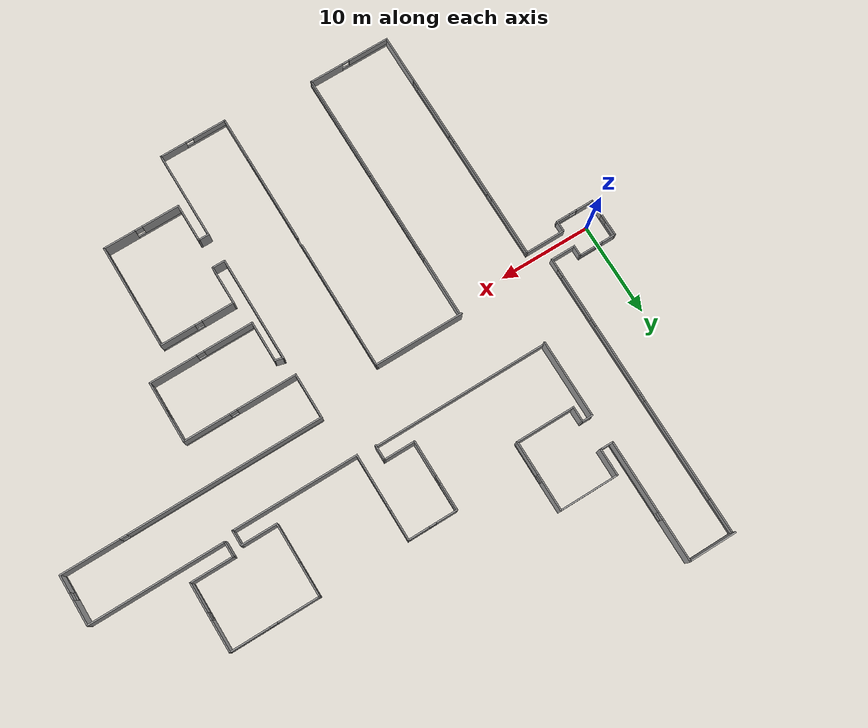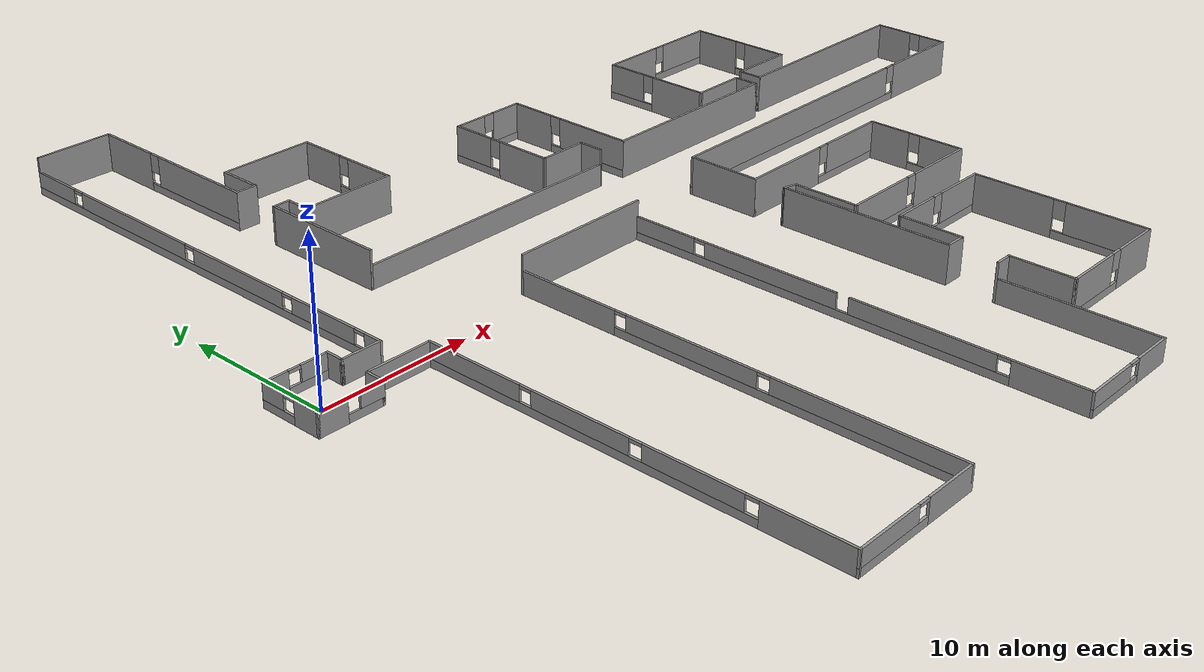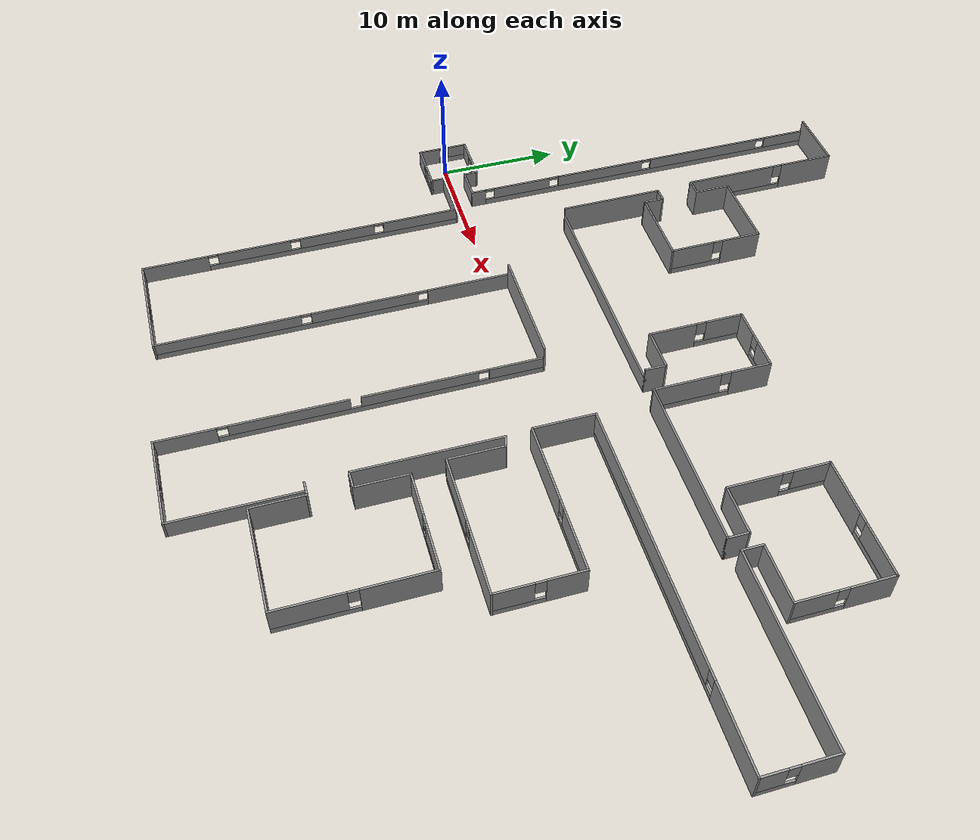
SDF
<?xml version='1.0'?>
<sdf version='1.7'>
  <model name='Hummanoid_Test_world'>
    <pose>29.59 2.105 0 0 -0 0</pose>
    <link name='Wall_1'>
      <pose>-29.1696 -3.935 0 0 -0 0</pose>
      <visual name='Wall_1_Visual_0'>
        <pose>-1.19344 0 0.75 0 -0 0</pose>
        <geometry>
          <box>
            <size>1.92395 0.15 1.5</size>
          </box>
        </geometry>
        <material>
          <script>
            <uri>file://media/materials/scripts/gazebo.material</uri>
            <name>Gazebo/Grey</name>
          </script>
          <ambient>1 1 1 1</ambient>
        </material>
        <meta>
          <layer>0</layer>
        </meta>
      </visual>
      <collision name='Wall_1_Collision_0'>
        <geometry>
          <box>
            <size>1.92395 0.15 1.5</size>
          </box>
        </geometry>
        <pose>-1.19344 0 0.75 0 -0 0</pose>
      </collision>
      <visual name='Wall_1_Visual_1'>
        <pose>0.961976 0 0.25 0 -0 0</pose>
        <geometry>
          <box>
            <size>2.38688 0.15 0.5</size>
          </box>
        </geometry>
        <material>
          <script>
            <uri>file://media/materials/scripts/gazebo.material</uri>
            <name>Gazebo/Grey</name>
          </script>
          <ambient>1 1 1 1</ambient>
        </material>
        <meta>
          <layer>0</layer>
        </meta>
      </visual>
      <collision name='Wall_1_Collision_1'>
        <geometry>
          <box>
            <size>2.38688 0.15 0.5</size>
          </box>
        </geometry>
        <pose>0.961976 0 0.25 0 -0 0</pose>
      </collision>
      <visual name='Wall_1_Visual_2'>
        <pose>1.36198 0 1 0 -0 0</pose>
        <geometry>
          <box>
            <size>1.58688 0.15 1</size>
          </box>
        </geometry>
        <material>
          <script>
            <uri>file://media/materials/scripts/gazebo.material</uri>
            <name>Gazebo/Grey</name>
          </script>
          <ambient>1 1 1 1</ambient>
        </material>
        <meta>
          <layer>0</layer>
        </meta>
      </visual>
      <collision name='Wall_1_Collision_2'>
        <geometry>
          <box>
            <size>1.58688 0.15 1</size>
          </box>
        </geometry>
        <pose>1.36198 0 1 0 -0 0</pose>
      </collision>
      <visual name='Wall_1_Visual_3'>
        <pose>0.168535 0 1.4 0 -0 0</pose>
        <geometry>
          <box>
            <size>0.8 0.15 0.2</size>
          </box>
        </geometry>
        <material>
          <script>
            <uri>file://media/materials/scripts/gazebo.material</uri>
            <name>Gazebo/Grey</name>
          </script>
          <ambient>1 1 1 1</ambient>
        </material>
        <meta>
          <layer>0</layer>
        </meta>
      </visual>
      <collision name='Wall_1_Collision_3'>
        <geometry>
          <box>
            <size>0.8 0.15 0.2</size>
          </box>
        </geometry>
        <pose>0.168535 0 1.4 0 -0 0</pose>
      </collision>
    </link>
    <link name='Wall_10'>
      <collision name='Wall_10_Collision'>
        <geometry>
          <box>
            <size>2.75 0.15 1.5</size>
          </box>
        </geometry>
        <pose>0 0 0.75 0 -0 0</pose>
      </collision>
      <visual name='Wall_10_Visual'>
        <pose>0 0 0.75 0 -0 0</pose>
        <geometry>
          <box>
            <size>2.75 0.15 1.5</size>
          </box>
        </geometry>
        <material>
          <script>
            <uri>file://media/materials/scripts/gazebo.material</uri>
            <name>Gazebo/Grey</name>
          </script>
          <ambient>1 1 1 1</ambient>
        </material>
        <meta>
          <layer>0</layer>
        </meta>
      </visual>
      <pose>-25.85 -0.935 0 0 -0 0</pose>
    </link>
    <link name='Wall_11'>
      <pose>-24.55 14.74 0 0 -0 1.5708</pose>
      <visual name='Wall_11_Visual_0'>
        <pose>-15.1239 0 0.75 0 -0 0</pose>
        <geometry>
          <box>
            <size>1.25227 0.15 1.5</size>
          </box>
        </geometry>
        <material>
          <script>
            <uri>file://media/materials/scripts/gazebo.material</uri>
            <name>Gazebo/Grey</name>
          </script>
          <ambient>1 1 1 1</ambient>
        </material>
        <meta>
          <layer>0</layer>
        </meta>
      </visual>
      <collision name='Wall_11_Collision_0'>
        <geometry>
          <box>
            <size>1.25227 0.15 1.5</size>
          </box>
        </geometry>
        <pose>-15.1239 0 0.75 0 -0 0</pose>
      </collision>
      <visual name='Wall_11_Visual_1'>
        <pose>0.626135 0 0.25 0 -0 0</pose>
        <geometry>
          <box>
            <size>30.2477 0.15 0.5</size>
          </box>
        </geometry>
        <material>
          <script>
            <uri>file://media/materials/scripts/gazebo.material</uri>
            <name>Gazebo/Grey</name>
          </script>
          <ambient>1 1 1 1</ambient>
        </material>
        <meta>
          <layer>0</layer>
        </meta>
      </visual>
      <collision name='Wall_11_Collision_1'>
        <geometry>
          <box>
            <size>30.2477 0.15 0.5</size>
          </box>
        </geometry>
        <pose>0.626135 0 0.25 0 -0 0</pose>
      </collision>
      <visual name='Wall_11_Visual_2'>
        <pose>-11.1577 0 1 0 -0 0</pose>
        <geometry>
          <box>
            <size>5.08 0.15 1</size>
          </box>
        </geometry>
        <material>
          <script>
            <uri>file://media/materials/scripts/gazebo.material</uri>
            <name>Gazebo/Grey</name>
          </script>
          <ambient>1 1 1 1</ambient>
        </material>
        <meta>
          <layer>0</layer>
        </meta>
      </visual>
      <collision name='Wall_11_Collision_2'>
        <geometry>
          <box>
            <size>5.08 0.15 1</size>
          </box>
        </geometry>
        <pose>-11.1577 0 1 0 -0 0</pose>
      </collision>
      <visual name='Wall_11_Visual_3'>
        <pose>-3.87047 0 1 0 -0 0</pose>
        <geometry>
          <box>
            <size>7.89451 0.15 1</size>
          </box>
        </geometry>
        <material>
          <script>
            <uri>file://media/materials/scripts/gazebo.material</uri>
            <name>Gazebo/Grey</name>
          </script>
          <ambient>1 1 1 1</ambient>
        </material>
        <meta>
          <layer>0</layer>
        </meta>
      </visual>
      <collision name='Wall_11_Collision_3'>
        <geometry>
          <box>
            <size>7.89451 0.15 1</size>
          </box>
        </geometry>
        <pose>-3.87047 0 1 0 -0 0</pose>
      </collision>
      <visual name='Wall_11_Visual_4'>
        <pose>6.00999 0 1 0 -0 0</pose>
        <geometry>
          <box>
            <size>10.2664 0.15 1</size>
          </box>
        </geometry>
        <material>
          <script>
            <uri>file://media/materials/scripts/gazebo.material</uri>
            <name>Gazebo/Grey</name>
          </script>
          <ambient>1 1 1 1</ambient>
        </material>
        <meta>
          <layer>0</layer>
        </meta>
      </visual>
      <collision name='Wall_11_Collision_4'>
        <geometry>
          <box>
            <size>10.2664 0.15 1</size>
          </box>
        </geometry>
        <pose>6.00999 0 1 0 -0 0</pose>
      </collision>
      <visual name='Wall_11_Visual_5'>
        <pose>13.8466 0 1 0 -0 0</pose>
        <geometry>
          <box>
            <size>3.80681 0.15 1</size>
          </box>
        </geometry>
        <material>
          <script>
            <uri>file://media/materials/scripts/gazebo.material</uri>
            <name>Gazebo/Grey</name>
          </script>
          <ambient>1 1 1 1</ambient>
        </material>
        <meta>
          <layer>0</layer>
        </meta>
      </visual>
      <collision name='Wall_11_Collision_5'>
        <geometry>
          <box>
            <size>3.80681 0.15 1</size>
          </box>
        </geometry>
        <pose>13.8466 0 1 0 -0 0</pose>
      </collision>
      <visual name='Wall_11_Visual_6'>
        <pose>-14.0977 0 1.4 0 -0 0</pose>
        <geometry>
          <box>
            <size>0.8 0.15 0.2</size>
          </box>
        </geometry>
        <material>
          <script>
            <uri>file://media/materials/scripts/gazebo.material</uri>
            <name>Gazebo/Grey</name>
          </script>
          <ambient>1 1 1 1</ambient>
        </material>
        <meta>
          <layer>0</layer>
        </meta>
      </visual>
      <collision name='Wall_11_Collision_6'>
        <geometry>
          <box>
            <size>0.8 0.15 0.2</size>
          </box>
        </geometry>
        <pose>-14.0977 0 1.4 0 -0 0</pose>
      </collision>
      <visual name='Wall_11_Visual_7'>
        <pose>-8.21773 0 1.4 0 -0 0</pose>
        <geometry>
          <box>
            <size>0.8 0.15 0.2</size>
          </box>
        </geometry>
        <material>
          <script>
            <uri>file://media/materials/scripts/gazebo.material</uri>
            <name>Gazebo/Grey</name>
          </script>
          <ambient>1 1 1 1</ambient>
        </material>
        <meta>
          <layer>0</layer>
        </meta>
      </visual>
      <collision name='Wall_11_Collision_7'>
        <geometry>
          <box>
            <size>0.8 0.15 0.2</size>
          </box>
        </geometry>
        <pose>-8.21773 0 1.4 0 -0 0</pose>
      </collision>
      <visual name='Wall_11_Visual_8'>
        <pose>0.476782 0 1.4 0 -0 0</pose>
        <geometry>
          <box>
            <size>0.8 0.15 0.2</size>
          </box>
        </geometry>
        <material>
          <script>
            <uri>file://media/materials/scripts/gazebo.material</uri>
            <name>Gazebo/Grey</name>
          </script>
          <ambient>1 1 1 1</ambient>
        </material>
        <meta>
          <layer>0</layer>
        </meta>
      </visual>
      <collision name='Wall_11_Collision_8'>
        <geometry>
          <box>
            <size>0.8 0.15 0.2</size>
          </box>
        </geometry>
        <pose>0.476782 0 1.4 0 -0 0</pose>
      </collision>
      <visual name='Wall_11_Visual_9'>
        <pose>11.5432 0 1.4 0 -0 0</pose>
        <geometry>
          <box>
            <size>0.8 0.15 0.2</size>
          </box>
        </geometry>
        <material>
          <script>
            <uri>file://media/materials/scripts/gazebo.material</uri>
            <name>Gazebo/Grey</name>
          </script>
          <ambient>1 1 1 1</ambient>
        </material>
        <meta>
          <layer>0</layer>
        </meta>
      </visual>
      <collision name='Wall_11_Collision_9'>
        <geometry>
          <box>
            <size>0.8 0.15 0.2</size>
          </box>
        </geometry>
        <pose>11.5432 0 1.4 0 -0 0</pose>
      </collision>
    </link>
    <link name='Wall_12'>
      <collision name='Wall_12_Collision'>
        <geometry>
          <box>
            <size>5.25 0.15 2.5</size>
          </box>
        </geometry>
        <pose>0 0 1.25 0 -0 0</pose>
      </collision>
      <visual name='Wall_12_Visual'>
        <pose>0 0 1.25 0 -0 0</pose>
        <geometry>
          <box>
            <size>5.25 0.15 2.5</size>
          </box>
        </geometry>
        <material>
          <script>
            <uri>file://media/materials/scripts/gazebo.material</uri>
            <name>Gazebo/Grey</name>
          </script>
          <ambient>1 1 1 1</ambient>
        </material>
        <meta>
          <layer>0</layer>
        </meta>
      </visual>
      <pose>-22 30.415 0 0 -0 0</pose>
    </link>
    <link name='Wall_13'>
      <pose>-19.45 23.865 0 0 -0 -1.5708</pose>
      <visual name='Wall_13_Visual_0'>
        <pose>-4.31474 0 1.25 0 -0 0</pose>
        <geometry>
          <box>
            <size>4.62052 0.15 2.5</size>
          </box>
        </geometry>
        <material>
          <script>
            <uri>file://media/materials/scripts/gazebo.material</uri>
            <name>Gazebo/Grey</name>
          </script>
          <ambient>1 1 1 1</ambient>
        </material>
        <meta>
          <layer>0</layer>
        </meta>
      </visual>
      <collision name='Wall_13_Collision_0'>
        <geometry>
          <box>
            <size>4.62052 0.15 2.5</size>
          </box>
        </geometry>
        <pose>-4.31474 0 1.25 0 -0 0</pose>
      </collision>
      <visual name='Wall_13_Visual_1'>
        <pose>2.31026 0 0.25 0 -0 0</pose>
        <geometry>
          <box>
            <size>8.62948 0.15 0.5</size>
          </box>
        </geometry>
        <material>
          <script>
            <uri>file://media/materials/scripts/gazebo.material</uri>
            <name>Gazebo/Grey</name>
          </script>
          <ambient>1 1 1 1</ambient>
        </material>
        <meta>
          <layer>0</layer>
        </meta>
      </visual>
      <collision name='Wall_13_Collision_1'>
        <geometry>
          <box>
            <size>8.62948 0.15 0.5</size>
          </box>
        </geometry>
        <pose>2.31026 0 0.25 0 -0 0</pose>
      </collision>
      <visual name='Wall_13_Visual_2'>
        <pose>2.71026 0 1.5 0 -0 0</pose>
        <geometry>
          <box>
            <size>7.82948 0.15 2</size>
          </box>
        </geometry>
        <material>
          <script>
            <uri>file://media/materials/scripts/gazebo.material</uri>
            <name>Gazebo/Grey</name>
          </script>
          <ambient>1 1 1 1</ambient>
        </material>
        <meta>
          <layer>0</layer>
        </meta>
      </visual>
      <collision name='Wall_13_Collision_2'>
        <geometry>
          <box>
            <size>7.82948 0.15 2</size>
          </box>
        </geometry>
        <pose>2.71026 0 1.5 0 -0 0</pose>
      </collision>
      <visual name='Wall_13_Visual_3'>
        <pose>-1.60448 0 1.9 0 -0 0</pose>
        <geometry>
          <box>
            <size>0.8 0.15 1.2</size>
          </box>
        </geometry>
        <material>
          <script>
            <uri>file://media/materials/scripts/gazebo.material</uri>
            <name>Gazebo/Grey</name>
          </script>
          <ambient>1 1 1 1</ambient>
        </material>
        <meta>
          <layer>0</layer>
        </meta>
      </visual>
      <collision name='Wall_13_Collision_3'>
        <geometry>
          <box>
            <size>0.8 0.15 1.2</size>
          </box>
        </geometry>
        <pose>-1.60448 0 1.9 0 -0 0</pose>
      </collision>
    </link>
    <link name='Wall_17'>
      <collision name='Wall_17_Collision'>
        <geometry>
          <box>
            <size>1.5 0.15 2.5</size>
          </box>
        </geometry>
        <pose>0 0 1.25 0 -0 0</pose>
      </collision>
      <visual name='Wall_17_Visual'>
        <pose>0 0 1.25 0 -0 0</pose>
        <geometry>
          <box>
            <size>1.5 0.15 2.5</size>
          </box>
        </geometry>
        <material>
          <script>
            <uri>file://media/materials/scripts/gazebo.material</uri>
            <name>Gazebo/Grey</name>
          </script>
          <ambient>1 1 1 1</ambient>
        </material>
        <meta>
          <layer>0</layer>
        </meta>
      </visual>
      <pose>-18.775 17.315 0 0 -0 0</pose>
    </link>
    <link name='Wall_18'>
      <collision name='Wall_18_Collision'>
        <geometry>
          <box>
            <size>3 0.15 2.5</size>
          </box>
        </geometry>
        <pose>0 0 1.25 0 -0 0</pose>
      </collision>
      <visual name='Wall_18_Visual'>
        <pose>0 0 1.25 0 -0 0</pose>
        <geometry>
          <box>
            <size>3 0.15 2.5</size>
          </box>
        </geometry>
        <material>
          <script>
            <uri>file://media/materials/scripts/gazebo.material</uri>
            <name>Gazebo/Grey</name>
          </script>
          <ambient>1 1 1 1</ambient>
        </material>
        <meta>
          <layer>0</layer>
        </meta>
      </visual>
      <pose>-18.1 18.74 0 0 -0 1.5708</pose>
    </link>
    <link name='Wall_19'>
      <collision name='Wall_19_Collision'>
        <geometry>
          <box>
            <size>6.5 0.15 2.5</size>
          </box>
        </geometry>
        <pose>0 0 1.25 0 -0 0</pose>
      </collision>
      <visual name='Wall_19_Visual'>
        <pose>0 0 1.25 0 -0 0</pose>
        <geometry>
          <box>
            <size>6.5 0.15 2.5</size>
          </box>
        </geometry>
        <material>
          <script>
            <uri>file://media/materials/scripts/gazebo.material</uri>
            <name>Gazebo/Grey</name>
          </script>
          <ambient>1 1 1 1</ambient>
        </material>
        <meta>
          <layer>0</layer>
        </meta>
      </visual>
      <pose>-14.925 20.165 0 0 -0 0</pose>
    </link>
    <link name='Wall_20'>
      <pose>-11.75 16.365 0 0 -0 -1.5708</pose>
      <visual name='Wall_20_Visual_0'>
        <pose>-2.24729 0 1.25 0 -0 0</pose>
        <geometry>
          <box>
            <size>3.25542 0.15 2.5</size>
          </box>
        </geometry>
        <material>
          <script>
            <uri>file://media/materials/scripts/gazebo.material</uri>
            <name>Gazebo/Grey</name>
          </script>
          <ambient>1 1 1 1</ambient>
        </material>
        <meta>
          <layer>0</layer>
        </meta>
      </visual>
      <collision name='Wall_20_Collision_0'>
        <geometry>
          <box>
            <size>3.25542 0.15 2.5</size>
          </box>
        </geometry>
        <pose>-2.24729 0 1.25 0 -0 0</pose>
      </collision>
      <visual name='Wall_20_Visual_1'>
        <pose>1.62771 0 0.25 0 -0 0</pose>
        <geometry>
          <box>
            <size>4.49458 0.15 0.5</size>
          </box>
        </geometry>
        <material>
          <script>
            <uri>file://media/materials/scripts/gazebo.material</uri>
            <name>Gazebo/Grey</name>
          </script>
          <ambient>1 1 1 1</ambient>
        </material>
        <meta>
          <layer>0</layer>
        </meta>
      </visual>
      <collision name='Wall_20_Collision_1'>
        <geometry>
          <box>
            <size>4.49458 0.15 0.5</size>
          </box>
        </geometry>
        <pose>1.62771 0 0.25 0 -0 0</pose>
      </collision>
      <visual name='Wall_20_Visual_2'>
        <pose>2.02771 0 1.5 0 -0 0</pose>
        <geometry>
          <box>
            <size>3.69458 0.15 2</size>
          </box>
        </geometry>
        <material>
          <script>
            <uri>file://media/materials/scripts/gazebo.material</uri>
            <name>Gazebo/Grey</name>
          </script>
          <ambient>1 1 1 1</ambient>
        </material>
        <meta>
          <layer>0</layer>
        </meta>
      </visual>
      <collision name='Wall_20_Collision_2'>
        <geometry>
          <box>
            <size>3.69458 0.15 2</size>
          </box>
        </geometry>
        <pose>2.02771 0 1.5 0 -0 0</pose>
      </collision>
      <visual name='Wall_20_Visual_3'>
        <pose>-0.219584 0 1.9 0 -0 0</pose>
        <geometry>
          <box>
            <size>0.8 0.15 1.2</size>
          </box>
        </geometry>
        <material>
          <script>
            <uri>file://media/materials/scripts/gazebo.material</uri>
            <name>Gazebo/Grey</name>
          </script>
          <ambient>1 1 1 1</ambient>
        </material>
        <meta>
          <layer>0</layer>
        </meta>
      </visual>
      <collision name='Wall_20_Collision_3'>
        <geometry>
          <box>
            <size>0.8 0.15 1.2</size>
          </box>
        </geometry>
        <pose>-0.219584 0 1.9 0 -0 0</pose>
      </collision>
    </link>
    <link name='Wall_21'>
      <collision name='Wall_21_Collision'>
        <geometry>
          <box>
            <size>6.5 0.15 2.5</size>
          </box>
        </geometry>
        <pose>0 0 1.25 0 -0 0</pose>
      </collision>
      <visual name='Wall_21_Visual'>
        <pose>0 0 1.25 0 -0 0</pose>
        <geometry>
          <box>
            <size>6.5 0.15 2.5</size>
          </box>
        </geometry>
        <material>
          <script>
            <uri>file://media/materials/scripts/gazebo.material</uri>
            <name>Gazebo/Grey</name>
          </script>
          <ambient>1 1 1 1</ambient>
        </material>
        <meta>
          <layer>0</layer>
        </meta>
      </visual>
      <pose>-14.925 12.565 0 0 -0 3.14159</pose>
    </link>
    <link name='Wall_22'>
      <collision name='Wall_22_Collision'>
        <geometry>
          <box>
            <size>1.75 0.15 2.5</size>
          </box>
        </geometry>
        <pose>0 0 1.25 0 -0 0</pose>
      </collision>
      <visual name='Wall_22_Visual'>
        <pose>0 0 1.25 0 -0 0</pose>
        <geometry>
          <box>
            <size>1.75 0.15 2.5</size>
          </box>
        </geometry>
        <material>
          <script>
            <uri>file://media/materials/scripts/gazebo.material</uri>
            <name>Gazebo/Grey</name>
          </script>
          <ambient>1 1 1 1</ambient>
        </material>
        <meta>
          <layer>0</layer>
        </meta>
      </visual>
      <pose>-18.1 13.365 0 0 -0 1.5708</pose>
    </link>
    <link name='Wall_23'>
      <collision name='Wall_23_Collision'>
        <geometry>
          <box>
            <size>1.25 0.15 2.5</size>
          </box>
        </geometry>
        <pose>0 0 1.25 0 -0 0</pose>
      </collision>
      <visual name='Wall_23_Visual'>
        <pose>0 0 1.25 0 -0 0</pose>
        <geometry>
          <box>
            <size>1.25 0.15 2.5</size>
          </box>
        </geometry>
        <material>
          <script>
            <uri>file://media/materials/scripts/gazebo.material</uri>
            <name>Gazebo/Grey</name>
          </script>
          <ambient>1 1 1 1</ambient>
        </material>
        <meta>
          <layer>0</layer>
        </meta>
      </visual>
      <pose>-18.65 14.165 0 0 -0 3.14159</pose>
    </link>
    <link name='Wall_24'>
      <collision name='Wall_24_Collision'>
        <geometry>
          <box>
            <size>8.5 0.15 2.5</size>
          </box>
        </geometry>
        <pose>0 0 1.25 0 -0 0</pose>
      </collision>
      <visual name='Wall_24_Visual'>
        <pose>0 0 1.25 0 -0 0</pose>
        <geometry>
          <box>
            <size>8.5 0.15 2.5</size>
          </box>
        </geometry>
        <material>
          <script>
            <uri>file://media/materials/scripts/gazebo.material</uri>
            <name>Gazebo/Grey</name>
          </script>
          <ambient>1 1 1 1</ambient>
        </material>
        <meta>
          <layer>0</layer>
        </meta>
      </visual>
      <pose>-19.2 9.99 0 0 -0 -1.5708</pose>
    </link>
    <link name='Wall_25'>
      <collision name='Wall_25_Collision'>
        <geometry>
          <box>
            <size>19.25 0.15 1.5</size>
          </box>
        </geometry>
        <pose>0 0 0.75 0 -0 0</pose>
      </collision>
      <visual name='Wall_25_Visual'>
        <pose>0 0 0.75 0 -0 0</pose>
        <geometry>
          <box>
            <size>19.25 0.15 1.5</size>
          </box>
        </geometry>
        <material>
          <script>
            <uri>file://media/materials/scripts/gazebo.material</uri>
            <name>Gazebo/Grey</name>
          </script>
          <ambient>1 1 1 1</ambient>
        </material>
        <meta>
          <layer>0</layer>
        </meta>
      </visual>
      <pose>-9.65 5.815 0 0 -0 0</pose>
    </link>
    <link name='Wall_26'>
      <collision name='Wall_26_Collision'>
        <geometry>
          <box>
            <size>1.75 0.15 2.5</size>
          </box>
        </geometry>
        <pose>0 0 1.25 0 -0 0</pose>
      </collision>
      <visual name='Wall_26_Visual'>
        <pose>0 0 1.25 0 -0 0</pose>
        <geometry>
          <box>
            <size>1.75 0.15 2.5</size>
          </box>
        </geometry>
        <material>
          <script>
            <uri>file://media/materials/scripts/gazebo.material</uri>
            <name>Gazebo/Grey</name>
          </script>
          <ambient>1 1 1 1</ambient>
        </material>
        <meta>
          <layer>0</layer>
        </meta>
      </visual>
      <pose>-0.100001 6.615 0 0 -0 1.5708</pose>
    </link>
    <link name='Wall_27'>
      <collision name='Wall_27_Collision'>
        <geometry>
          <box>
            <size>3.5 0.15 2.5</size>
          </box>
        </geometry>
        <pose>0 0 1.25 0 -0 0</pose>
      </collision>
      <visual name='Wall_27_Visual'>
        <pose>0 0 1.25 0 -0 0</pose>
        <geometry>
          <box>
            <size>3.5 0.15 2.5</size>
          </box>
        </geometry>
        <material>
          <script>
            <uri>file://media/materials/scripts/gazebo.material</uri>
            <name>Gazebo/Grey</name>
          </script>
          <ambient>1 1 1 1</ambient>
        </material>
        <meta>
          <layer>0</layer>
        </meta>
      </visual>
      <pose>-1.775 7.415 0 0 -0 3.14159</pose>
    </link>
    <link name='Wall_28'>
      <pose>-3.45 11.215 0 0 -0 1.5708</pose>
      <visual name='Wall_28_Visual_0'>
        <pose>-1.91382 0 1.25 0 -0 0</pose>
        <geometry>
          <box>
            <size>3.92235 0.15 2.5</size>
          </box>
        </geometry>
        <material>
          <script>
            <uri>file://media/materials/scripts/gazebo.material</uri>
            <name>Gazebo/Grey</name>
          </script>
          <ambient>1 1 1 1</ambient>
        </material>
        <meta>
          <layer>0</layer>
        </meta>
      </visual>
      <collision name='Wall_28_Collision_0'>
        <geometry>
          <box>
            <size>3.92235 0.15 2.5</size>
          </box>
        </geometry>
        <pose>-1.91382 0 1.25 0 -0 0</pose>
      </collision>
      <visual name='Wall_28_Visual_1'>
        <pose>1.96118 0 0.25 0 -0 0</pose>
        <geometry>
          <box>
            <size>3.82765 0.15 0.5</size>
          </box>
        </geometry>
        <material>
          <script>
            <uri>file://media/materials/scripts/gazebo.material</uri>
            <name>Gazebo/Grey</name>
          </script>
          <ambient>1 1 1 1</ambient>
        </material>
        <meta>
          <layer>0</layer>
        </meta>
      </visual>
      <collision name='Wall_28_Collision_1'>
        <geometry>
          <box>
            <size>3.82765 0.15 0.5</size>
          </box>
        </geometry>
        <pose>1.96118 0 0.25 0 -0 0</pose>
      </collision>
      <visual name='Wall_28_Visual_2'>
        <pose>2.36118 0 1.5 0 -0 0</pose>
        <geometry>
          <box>
            <size>3.02765 0.15 2</size>
          </box>
        </geometry>
        <material>
          <script>
            <uri>file://media/materials/scripts/gazebo.material</uri>
            <name>Gazebo/Grey</name>
          </script>
          <ambient>1 1 1 1</ambient>
        </material>
        <meta>
          <layer>0</layer>
        </meta>
      </visual>
      <collision name='Wall_28_Collision_2'>
        <geometry>
          <box>
            <size>3.02765 0.15 2</size>
          </box>
        </geometry>
        <pose>2.36118 0 1.5 0 -0 0</pose>
      </collision>
      <visual name='Wall_28_Visual_3'>
        <pose>0.447352 0 1.9 0 -0 0</pose>
        <geometry>
          <box>
            <size>0.8 0.15 1.2</size>
          </box>
        </geometry>
        <material>
          <script>
            <uri>file://media/materials/scripts/gazebo.material</uri>
            <name>Gazebo/Grey</name>
          </script>
          <ambient>1 1 1 1</ambient>
        </material>
        <meta>
          <layer>0</layer>
        </meta>
      </visual>
      <collision name='Wall_28_Collision_3'>
        <geometry>
          <box>
            <size>0.8 0.15 1.2</size>
          </box>
        </geometry>
        <pose>0.447352 0 1.9 0 -0 0</pose>
      </collision>
    </link>
    <link name='Wall_29'>
      <pose>-0.775 15.015 0 0 -0 0</pose>
      <visual name='Wall_29_Visual_0'>
        <pose>-1.5701 0 1.25 0 -0 0</pose>
        <geometry>
          <box>
            <size>2.35979 0.15 2.5</size>
          </box>
        </geometry>
        <material>
          <script>
            <uri>file://media/materials/scripts/gazebo.material</uri>
            <name>Gazebo/Grey</name>
          </script>
          <ambient>1 1 1 1</ambient>
        </material>
        <meta>
          <layer>0</layer>
        </meta>
      </visual>
      <collision name='Wall_29_Collision_0'>
        <geometry>
          <box>
            <size>2.35979 0.15 2.5</size>
          </box>
        </geometry>
        <pose>-1.5701 0 1.25 0 -0 0</pose>
      </collision>
      <visual name='Wall_29_Visual_1'>
        <pose>1.1799 0 0.25 0 -0 0</pose>
        <geometry>
          <box>
            <size>3.14021 0.15 0.5</size>
          </box>
        </geometry>
        <material>
          <script>
            <uri>file://media/materials/scripts/gazebo.material</uri>
            <name>Gazebo/Grey</name>
          </script>
          <ambient>1 1 1 1</ambient>
        </material>
        <meta>
          <layer>0</layer>
        </meta>
      </visual>
      <collision name='Wall_29_Collision_1'>
        <geometry>
          <box>
            <size>3.14021 0.15 0.5</size>
          </box>
        </geometry>
        <pose>1.1799 0 0.25 0 -0 0</pose>
      </collision>
      <visual name='Wall_29_Visual_2'>
        <pose>1.5799 0 1.5 0 -0 0</pose>
        <geometry>
          <box>
            <size>2.34021 0.15 2</size>
          </box>
        </geometry>
        <material>
          <script>
            <uri>file://media/materials/scripts/gazebo.material</uri>
            <name>Gazebo/Grey</name>
          </script>
          <ambient>1 1 1 1</ambient>
        </material>
        <meta>
          <layer>0</layer>
        </meta>
      </visual>
      <collision name='Wall_29_Collision_2'>
        <geometry>
          <box>
            <size>2.34021 0.15 2</size>
          </box>
        </geometry>
        <pose>1.5799 0 1.5 0 -0 0</pose>
      </collision>
      <visual name='Wall_29_Visual_3'>
        <pose>0.009794 0 1.9 0 -0 0</pose>
        <geometry>
          <box>
            <size>0.8 0.15 1.2</size>
          </box>
        </geometry>
        <material>
          <script>
            <uri>file://media/materials/scripts/gazebo.material</uri>
            <name>Gazebo/Grey</name>
          </script>
          <ambient>1 1 1 1</ambient>
        </material>
        <meta>
          <layer>0</layer>
        </meta>
      </visual>
      <collision name='Wall_29_Collision_3'>
        <geometry>
          <box>
            <size>0.8 0.15 1.2</size>
          </box>
        </geometry>
        <pose>0.009794 0 1.9 0 -0 0</pose>
      </collision>
    </link>
    <link name='Wall_30'>
      <pose>1.9 10.34 0 0 -0 -1.5708</pose>
      <visual name='Wall_30_Visual_0'>
        <pose>-3.12917 0 1.25 0 -0 0</pose>
        <geometry>
          <box>
            <size>3.24166 0.15 2.5</size>
          </box>
        </geometry>
        <material>
          <script>
            <uri>file://media/materials/scripts/gazebo.material</uri>
            <name>Gazebo/Grey</name>
          </script>
          <ambient>1 1 1 1</ambient>
        </material>
        <meta>
          <layer>0</layer>
        </meta>
      </visual>
      <collision name='Wall_30_Collision_0'>
        <geometry>
          <box>
            <size>3.24166 0.15 2.5</size>
          </box>
        </geometry>
        <pose>-3.12917 0 1.25 0 -0 0</pose>
      </collision>
      <visual name='Wall_30_Visual_1'>
        <pose>1.62083 0 0.25 0 -0 0</pose>
        <geometry>
          <box>
            <size>6.25834 0.15 0.5</size>
          </box>
        </geometry>
        <material>
          <script>
            <uri>file://media/materials/scripts/gazebo.material</uri>
            <name>Gazebo/Grey</name>
          </script>
          <ambient>1 1 1 1</ambient>
        </material>
        <meta>
          <layer>0</layer>
        </meta>
      </visual>
      <collision name='Wall_30_Collision_1'>
        <geometry>
          <box>
            <size>6.25834 0.15 0.5</size>
          </box>
        </geometry>
        <pose>1.62083 0 0.25 0 -0 0</pose>
      </collision>
      <visual name='Wall_30_Visual_2'>
        <pose>2.02083 0 1.5 0 -0 0</pose>
        <geometry>
          <box>
            <size>5.45834 0.15 2</size>
          </box>
        </geometry>
        <material>
          <script>
            <uri>file://media/materials/scripts/gazebo.material</uri>
            <name>Gazebo/Grey</name>
          </script>
          <ambient>1 1 1 1</ambient>
        </material>
        <meta>
          <layer>0</layer>
        </meta>
      </visual>
      <collision name='Wall_30_Collision_2'>
        <geometry>
          <box>
            <size>5.45834 0.15 2</size>
          </box>
        </geometry>
        <pose>2.02083 0 1.5 0 -0 0</pose>
      </collision>
      <visual name='Wall_30_Visual_3'>
        <pose>-1.10834 0 1.9 0 -0 0</pose>
        <geometry>
          <box>
            <size>0.8 0.15 1.2</size>
          </box>
        </geometry>
        <material>
          <script>
            <uri>file://media/materials/scripts/gazebo.material</uri>
            <name>Gazebo/Grey</name>
          </script>
          <ambient>1 1 1 1</ambient>
        </material>
        <meta>
          <layer>0</layer>
        </meta>
      </visual>
      <collision name='Wall_30_Collision_3'>
        <geometry>
          <box>
            <size>0.8 0.15 1.2</size>
          </box>
        </geometry>
        <pose>-1.10834 0 1.9 0 -0 0</pose>
      </collision>
    </link>
    <link name='Wall_31'>
      <collision name='Wall_31_Collision'>
        <geometry>
          <box>
            <size>13.75 0.15 2.5</size>
          </box>
        </geometry>
        <pose>0 0 1.25 0 -0 0</pose>
      </collision>
      <visual name='Wall_31_Visual'>
        <pose>0 0 1.25 0 -0 0</pose>
        <geometry>
          <box>
            <size>13.75 0.15 2.5</size>
          </box>
        </geometry>
        <material>
          <script>
            <uri>file://media/materials/scripts/gazebo.material</uri>
            <name>Gazebo/Grey</name>
          </script>
          <ambient>1 1 1 1</ambient>
        </material>
        <meta>
          <layer>0</layer>
        </meta>
      </visual>
      <pose>8.7 5.665 0 0 -0 0</pose>
    </link>
    <link name='Wall_32'>
      <collision name='Wall_32_Collision'>
        <geometry>
          <box>
            <size>1.75 0.15 2.5</size>
          </box>
        </geometry>
        <pose>0 0 1.25 0 -0 0</pose>
      </collision>
      <visual name='Wall_32_Visual'>
        <pose>0 0 1.25 0 -0 0</pose>
        <geometry>
          <box>
            <size>1.75 0.15 2.5</size>
          </box>
        </geometry>
        <material>
          <script>
            <uri>file://media/materials/scripts/gazebo.material</uri>
            <name>Gazebo/Grey</name>
          </script>
          <ambient>1 1 1 1</ambient>
        </material>
        <meta>
          <layer>0</layer>
        </meta>
      </visual>
      <pose>15.5 6.465 0 0 -0 1.5708</pose>
    </link>
    <link name='Wall_33'>
      <collision name='Wall_33_Collision'>
        <geometry>
          <box>
            <size>4 0.15 2.5</size>
          </box>
        </geometry>
        <pose>0 0 1.25 0 -0 0</pose>
      </collision>
      <visual name='Wall_33_Visual'>
        <pose>0 0 1.25 0 -0 0</pose>
        <geometry>
          <box>
            <size>4 0.15 2.5</size>
          </box>
        </geometry>
        <material>
          <script>
            <uri>file://media/materials/scripts/gazebo.material</uri>
            <name>Gazebo/Grey</name>
          </script>
          <ambient>1 1 1 1</ambient>
        </material>
        <meta>
          <layer>0</layer>
        </meta>
      </visual>
      <pose>13.575 7.265 0 0 -0 3.14159</pose>
    </link>
    <link name='Wall_34'>
      <pose>11.65 11.19 0 0 -0 1.5708</pose>
      <visual name='Wall_34_Visual_0'>
        <pose>-1.85682 0 1.25 0 -0 0</pose>
        <geometry>
          <box>
            <size>4.28636 0.15 2.5</size>
          </box>
        </geometry>
        <material>
          <script>
            <uri>file://media/materials/scripts/gazebo.material</uri>
            <name>Gazebo/Grey</name>
          </script>
          <ambient>1 1 1 1</ambient>
        </material>
        <meta>
          <layer>0</layer>
        </meta>
      </visual>
      <collision name='Wall_34_Collision_0'>
        <geometry>
          <box>
            <size>4.28636 0.15 2.5</size>
          </box>
        </geometry>
        <pose>-1.85682 0 1.25 0 -0 0</pose>
      </collision>
      <visual name='Wall_34_Visual_1'>
        <pose>2.14318 0 0.25 0 -0 0</pose>
        <geometry>
          <box>
            <size>3.71364 0.15 0.5</size>
          </box>
        </geometry>
        <material>
          <script>
            <uri>file://media/materials/scripts/gazebo.material</uri>
            <name>Gazebo/Grey</name>
          </script>
          <ambient>1 1 1 1</ambient>
        </material>
        <meta>
          <layer>0</layer>
        </meta>
      </visual>
      <collision name='Wall_34_Collision_1'>
        <geometry>
          <box>
            <size>3.71364 0.15 0.5</size>
          </box>
        </geometry>
        <pose>2.14318 0 0.25 0 -0 0</pose>
      </collision>
      <visual name='Wall_34_Visual_2'>
        <pose>2.54318 0 1.5 0 -0 0</pose>
        <geometry>
          <box>
            <size>2.91364 0.15 2</size>
          </box>
        </geometry>
        <material>
          <script>
            <uri>file://media/materials/scripts/gazebo.material</uri>
            <name>Gazebo/Grey</name>
          </script>
          <ambient>1 1 1 1</ambient>
        </material>
        <meta>
          <layer>0</layer>
        </meta>
      </visual>
      <collision name='Wall_34_Collision_2'>
        <geometry>
          <box>
            <size>2.91364 0.15 2</size>
          </box>
        </geometry>
        <pose>2.54318 0 1.5 0 -0 0</pose>
      </collision>
      <visual name='Wall_34_Visual_3'>
        <pose>0.686362 0 1.9 0 -0 0</pose>
        <geometry>
          <box>
            <size>0.8 0.15 1.2</size>
          </box>
        </geometry>
        <material>
          <script>
            <uri>file://media/materials/scripts/gazebo.material</uri>
            <name>Gazebo/Grey</name>
          </script>
          <ambient>1 1 1 1</ambient>
        </material>
        <meta>
          <layer>0</layer>
        </meta>
      </visual>
      <collision name='Wall_34_Collision_3'>
        <geometry>
          <box>
            <size>0.8 0.15 1.2</size>
          </box>
        </geometry>
        <pose>0.686362 0 1.9 0 -0 0</pose>
      </collision>
    </link>
    <link name='Wall_35'>
      <pose>16.45 15.115 0 0 -0 0</pose>
      <visual name='Wall_35_Visual_0'>
        <pose>-2.5777 0 1.25 0 -0 0</pose>
        <geometry>
          <box>
            <size>4.59461 0.15 2.5</size>
          </box>
        </geometry>
        <material>
          <script>
            <uri>file://media/materials/scripts/gazebo.material</uri>
            <name>Gazebo/Grey</name>
          </script>
          <ambient>1 1 1 1</ambient>
        </material>
        <meta>
          <layer>0</layer>
        </meta>
      </visual>
      <collision name='Wall_35_Collision_0'>
        <geometry>
          <box>
            <size>4.59461 0.15 2.5</size>
          </box>
        </geometry>
        <pose>-2.5777 0 1.25 0 -0 0</pose>
      </collision>
      <visual name='Wall_35_Visual_1'>
        <pose>2.2973 0 0.25 0 -0 0</pose>
        <geometry>
          <box>
            <size>5.15539 0.15 0.5</size>
          </box>
        </geometry>
        <material>
          <script>
            <uri>file://media/materials/scripts/gazebo.material</uri>
            <name>Gazebo/Grey</name>
          </script>
          <ambient>1 1 1 1</ambient>
        </material>
        <meta>
          <layer>0</layer>
        </meta>
      </visual>
      <collision name='Wall_35_Collision_1'>
        <geometry>
          <box>
            <size>5.15539 0.15 0.5</size>
          </box>
        </geometry>
        <pose>2.2973 0 0.25 0 -0 0</pose>
      </collision>
      <visual name='Wall_35_Visual_2'>
        <pose>2.6973 0 1.5 0 -0 0</pose>
        <geometry>
          <box>
            <size>4.35539 0.15 2</size>
          </box>
        </geometry>
        <material>
          <script>
            <uri>file://media/materials/scripts/gazebo.material</uri>
            <name>Gazebo/Grey</name>
          </script>
          <ambient>1 1 1 1</ambient>
        </material>
        <meta>
          <layer>0</layer>
        </meta>
      </visual>
      <collision name='Wall_35_Collision_2'>
        <geometry>
          <box>
            <size>4.35539 0.15 2</size>
          </box>
        </geometry>
        <pose>2.6973 0 1.5 0 -0 0</pose>
      </collision>
      <visual name='Wall_35_Visual_3'>
        <pose>0.119606 0 1.9 0 -0 0</pose>
        <geometry>
          <box>
            <size>0.8 0.15 1.2</size>
          </box>
        </geometry>
        <material>
          <script>
            <uri>file://media/materials/scripts/gazebo.material</uri>
            <name>Gazebo/Grey</name>
          </script>
          <ambient>1 1 1 1</ambient>
        </material>
        <meta>
          <layer>0</layer>
        </meta>
      </visual>
      <collision name='Wall_35_Collision_3'>
        <geometry>
          <box>
            <size>0.8 0.15 1.2</size>
          </box>
        </geometry>
        <pose>0.119606 0 1.9 0 -0 0</pose>
      </collision>
    </link>
    <link name='Wall_36'>
      <pose>21.25 11.44 0 0 -0 -1.5708</pose>
      <visual name='Wall_36_Visual_0'>
        <pose>-2.02567 0 1.25 0 -0 0</pose>
        <geometry>
          <box>
            <size>3.44866 0.15 2.5</size>
          </box>
        </geometry>
        <material>
          <script>
            <uri>file://media/materials/scripts/gazebo.material</uri>
            <name>Gazebo/Grey</name>
          </script>
          <ambient>1 1 1 1</ambient>
        </material>
        <meta>
          <layer>0</layer>
        </meta>
      </visual>
      <collision name='Wall_36_Collision_0'>
        <geometry>
          <box>
            <size>3.44866 0.15 2.5</size>
          </box>
        </geometry>
        <pose>-2.02567 0 1.25 0 -0 0</pose>
      </collision>
      <visual name='Wall_36_Visual_1'>
        <pose>1.72433 0 0.25 0 -0 0</pose>
        <geometry>
          <box>
            <size>4.05134 0.15 0.5</size>
          </box>
        </geometry>
        <material>
          <script>
            <uri>file://media/materials/scripts/gazebo.material</uri>
            <name>Gazebo/Grey</name>
          </script>
          <ambient>1 1 1 1</ambient>
        </material>
        <meta>
          <layer>0</layer>
        </meta>
      </visual>
      <collision name='Wall_36_Collision_1'>
        <geometry>
          <box>
            <size>4.05134 0.15 0.5</size>
          </box>
        </geometry>
        <pose>1.72433 0 0.25 0 -0 0</pose>
      </collision>
      <visual name='Wall_36_Visual_2'>
        <pose>2.12433 0 1.5 0 -0 0</pose>
        <geometry>
          <box>
            <size>3.25134 0.15 2</size>
          </box>
        </geometry>
        <material>
          <script>
            <uri>file://media/materials/scripts/gazebo.material</uri>
            <name>Gazebo/Grey</name>
          </script>
          <ambient>1 1 1 1</ambient>
        </material>
        <meta>
          <layer>0</layer>
        </meta>
      </visual>
      <collision name='Wall_36_Collision_2'>
        <geometry>
          <box>
            <size>3.25134 0.15 2</size>
          </box>
        </geometry>
        <pose>2.12433 0 1.5 0 -0 0</pose>
      </collision>
      <visual name='Wall_36_Visual_3'>
        <pose>0.098663 0 1.9 0 -0 0</pose>
        <geometry>
          <box>
            <size>0.8 0.15 1.2</size>
          </box>
        </geometry>
        <material>
          <script>
            <uri>file://media/materials/scripts/gazebo.material</uri>
            <name>Gazebo/Grey</name>
          </script>
          <ambient>1 1 1 1</ambient>
        </material>
        <meta>
          <layer>0</layer>
        </meta>
      </visual>
      <collision name='Wall_36_Collision_3'>
        <geometry>
          <box>
            <size>0.8 0.15 1.2</size>
          </box>
        </geometry>
        <pose>0.098663 0 1.9 0 -0 0</pose>
      </collision>
    </link>
    <link name='Wall_37'>
      <collision name='Wall_37_Collision'>
        <geometry>
          <box>
            <size>4.75 0.15 2.5</size>
          </box>
        </geometry>
        <pose>0 0 1.25 0 -0 0</pose>
      </collision>
      <visual name='Wall_37_Visual'>
        <pose>0 0 1.25 0 -0 0</pose>
        <geometry>
          <box>
            <size>4.75 0.15 2.5</size>
          </box>
        </geometry>
        <material>
          <script>
            <uri>file://media/materials/scripts/gazebo.material</uri>
            <name>Gazebo/Grey</name>
          </script>
          <ambient>1 1 1 1</ambient>
        </material>
        <meta>
          <layer>0</layer>
        </meta>
      </visual>
      <pose>18.95 7.765 0 0 -0 3.14159</pose>
    </link>
    <link name='Wall_38'>
      <collision name='Wall_38_Collision'>
        <geometry>
          <box>
            <size>1.75 0.15 2.5</size>
          </box>
        </geometry>
        <pose>0 0 1.25 0 -0 0</pose>
      </collision>
      <visual name='Wall_38_Visual'>
        <pose>0 0 1.25 0 -0 0</pose>
        <geometry>
          <box>
            <size>1.75 0.15 2.5</size>
          </box>
        </geometry>
        <material>
          <script>
            <uri>file://media/materials/scripts/gazebo.material</uri>
            <name>Gazebo/Grey</name>
          </script>
          <ambient>1 1 1 1</ambient>
        </material>
        <meta>
          <layer>0</layer>
        </meta>
      </visual>
      <pose>16.65 6.965 0 0 -0 -1.5708</pose>
    </link>
    <link name='Wall_39'>
      <collision name='Wall_39_Collision'>
        <geometry>
          <box>
            <size>14.75 0.15 2.5</size>
          </box>
        </geometry>
        <pose>0 0 1.25 0 -0 0</pose>
      </collision>
      <visual name='Wall_39_Visual'>
        <pose>0 0 1.25 0 -0 0</pose>
        <geometry>
          <box>
            <size>14.75 0.15 2.5</size>
          </box>
        </geometry>
        <material>
          <script>
            <uri>file://media/materials/scripts/gazebo.material</uri>
            <name>Gazebo/Grey</name>
          </script>
          <ambient>1 1 1 1</ambient>
        </material>
        <meta>
          <layer>0</layer>
        </meta>
      </visual>
      <pose>23.95 6.165 0 0 -0 0</pose>
    </link>
    <link name='Wall_4'>
      <pose>-31.25 -1.885 0 0 -0 1.5708</pose>
      <visual name='Wall_4_Visual_0'>
        <pose>-1.21756 0 0.75 0 -0 0</pose>
        <geometry>
          <box>
            <size>1.81488 0.15 1.5</size>
          </box>
        </geometry>
        <material>
          <script>
            <uri>file://media/materials/scripts/gazebo.material</uri>
            <name>Gazebo/Grey</name>
          </script>
          <ambient>1 1 1 1</ambient>
        </material>
        <meta>
          <layer>0</layer>
        </meta>
      </visual>
      <collision name='Wall_4_Collision_0'>
        <geometry>
          <box>
            <size>1.81488 0.15 1.5</size>
          </box>
        </geometry>
        <pose>-1.21756 0 0.75 0 -0 0</pose>
      </collision>
      <visual name='Wall_4_Visual_1'>
        <pose>0.907438 0 0.25 0 -0 0</pose>
        <geometry>
          <box>
            <size>2.43512 0.15 0.5</size>
          </box>
        </geometry>
        <material>
          <script>
            <uri>file://media/materials/scripts/gazebo.material</uri>
            <name>Gazebo/Grey</name>
          </script>
          <ambient>1 1 1 1</ambient>
        </material>
        <meta>
          <layer>0</layer>
        </meta>
      </visual>
      <collision name='Wall_4_Collision_1'>
        <geometry>
          <box>
            <size>2.43512 0.15 0.5</size>
          </box>
        </geometry>
        <pose>0.907438 0 0.25 0 -0 0</pose>
      </collision>
      <visual name='Wall_4_Visual_2'>
        <pose>1.30744 0 1 0 -0 0</pose>
        <geometry>
          <box>
            <size>1.63512 0.15 1</size>
          </box>
        </geometry>
        <material>
          <script>
            <uri>file://media/materials/scripts/gazebo.material</uri>
            <name>Gazebo/Grey</name>
          </script>
          <ambient>1 1 1 1</ambient>
        </material>
        <meta>
          <layer>0</layer>
        </meta>
      </visual>
      <collision name='Wall_4_Collision_2'>
        <geometry>
          <box>
            <size>1.63512 0.15 1</size>
          </box>
        </geometry>
        <pose>1.30744 0 1 0 -0 0</pose>
      </collision>
      <visual name='Wall_4_Visual_3'>
        <pose>0.089877 0 1.4 0 -0 0</pose>
        <geometry>
          <box>
            <size>0.8 0.15 0.2</size>
          </box>
        </geometry>
        <material>
          <script>
            <uri>file://media/materials/scripts/gazebo.material</uri>
            <name>Gazebo/Grey</name>
          </script>
          <ambient>1 1 1 1</ambient>
        </material>
        <meta>
          <layer>0</layer>
        </meta>
      </visual>
      <collision name='Wall_4_Collision_3'>
        <geometry>
          <box>
            <size>0.8 0.15 0.2</size>
          </box>
        </geometry>
        <pose>0.089877 0 1.4 0 -0 0</pose>
      </collision>
    </link>
    <link name='Wall_40'>
      <pose>31.25 3.49 0 0 -0 -1.5708</pose>
      <visual name='Wall_40_Visual_0'>
        <pose>-1.38098 0 1.25 0 -0 0</pose>
        <geometry>
          <box>
            <size>2.73805 0.15 2.5</size>
          </box>
        </geometry>
        <material>
          <script>
            <uri>file://media/materials/scripts/gazebo.material</uri>
            <name>Gazebo/Grey</name>
          </script>
          <ambient>1 1 1 1</ambient>
        </material>
        <meta>
          <layer>0</layer>
        </meta>
      </visual>
      <collision name='Wall_40_Collision_0'>
        <geometry>
          <box>
            <size>2.73805 0.15 2.5</size>
          </box>
        </geometry>
        <pose>-1.38098 0 1.25 0 -0 0</pose>
      </collision>
      <visual name='Wall_40_Visual_1'>
        <pose>1.36902 0 0.25 0 -0 0</pose>
        <geometry>
          <box>
            <size>2.76195 0.15 0.5</size>
          </box>
        </geometry>
        <material>
          <script>
            <uri>file://media/materials/scripts/gazebo.material</uri>
            <name>Gazebo/Grey</name>
          </script>
          <ambient>1 1 1 1</ambient>
        </material>
        <meta>
          <layer>0</layer>
        </meta>
      </visual>
      <collision name='Wall_40_Collision_1'>
        <geometry>
          <box>
            <size>2.76195 0.15 0.5</size>
          </box>
        </geometry>
        <pose>1.36902 0 0.25 0 -0 0</pose>
      </collision>
      <visual name='Wall_40_Visual_2'>
        <pose>1.76902 0 1.5 0 -0 0</pose>
        <geometry>
          <box>
            <size>1.96195 0.15 2</size>
          </box>
        </geometry>
        <material>
          <script>
            <uri>file://media/materials/scripts/gazebo.material</uri>
            <name>Gazebo/Grey</name>
          </script>
          <ambient>1 1 1 1</ambient>
        </material>
        <meta>
          <layer>0</layer>
        </meta>
      </visual>
      <collision name='Wall_40_Collision_2'>
        <geometry>
          <box>
            <size>1.96195 0.15 2</size>
          </box>
        </geometry>
        <pose>1.76902 0 1.5 0 -0 0</pose>
      </collision>
      <visual name='Wall_40_Visual_3'>
        <pose>0.388048 0 1.9 0 -0 0</pose>
        <geometry>
          <box>
            <size>0.8 0.15 1.2</size>
          </box>
        </geometry>
        <material>
          <script>
            <uri>file://media/materials/scripts/gazebo.material</uri>
            <name>Gazebo/Grey</name>
          </script>
          <ambient>1 1 1 1</ambient>
        </material>
        <meta>
          <layer>0</layer>
        </meta>
      </visual>
      <collision name='Wall_40_Collision_3'>
        <geometry>
          <box>
            <size>0.8 0.15 1.2</size>
          </box>
        </geometry>
        <pose>0.388048 0 1.9 0 -0 0</pose>
      </collision>
    </link>
    <link name='Wall_41'>
      <pose>17.075 0.815001 0 0 -0 3.14159</pose>
      <visual name='Wall_41_Visual_0'>
        <pose>-11.0315 0 1.25 0 -0 0</pose>
        <geometry>
          <box>
            <size>6.43703 0.15 2.5</size>
          </box>
        </geometry>
        <material>
          <script>
            <uri>file://media/materials/scripts/gazebo.material</uri>
            <name>Gazebo/Grey</name>
          </script>
          <ambient>1 1 1 1</ambient>
        </material>
        <meta>
          <layer>0</layer>
        </meta>
      </visual>
      <collision name='Wall_41_Collision_0'>
        <geometry>
          <box>
            <size>6.43703 0.15 2.5</size>
          </box>
        </geometry>
        <pose>-11.0315 0 1.25 0 -0 0</pose>
      </collision>
      <visual name='Wall_41_Visual_1'>
        <pose>3.21851 0 0.25 0 -0 0</pose>
        <geometry>
          <box>
            <size>22.063 0.15 0.5</size>
          </box>
        </geometry>
        <material>
          <script>
            <uri>file://media/materials/scripts/gazebo.material</uri>
            <name>Gazebo/Grey</name>
          </script>
          <ambient>1 1 1 1</ambient>
        </material>
        <meta>
          <layer>0</layer>
        </meta>
      </visual>
      <collision name='Wall_41_Collision_1'>
        <geometry>
          <box>
            <size>22.063 0.15 0.5</size>
          </box>
        </geometry>
        <pose>3.21851 0 0.25 0 -0 0</pose>
      </collision>
      <visual name='Wall_41_Visual_2'>
        <pose>3.61851 0 1.5 0 -0 0</pose>
        <geometry>
          <box>
            <size>21.263 0.15 2</size>
          </box>
        </geometry>
        <material>
          <script>
            <uri>file://media/materials/scripts/gazebo.material</uri>
            <name>Gazebo/Grey</name>
          </script>
          <ambient>1 1 1 1</ambient>
        </material>
        <meta>
          <layer>0</layer>
        </meta>
      </visual>
      <collision name='Wall_41_Collision_2'>
        <geometry>
          <box>
            <size>21.263 0.15 2</size>
          </box>
        </geometry>
        <pose>3.61851 0 1.5 0 -0 0</pose>
      </collision>
      <visual name='Wall_41_Visual_3'>
        <pose>-7.41298 0 1.9 0 -0 0</pose>
        <geometry>
          <box>
            <size>0.8 0.15 1.2</size>
          </box>
        </geometry>
        <material>
          <script>
            <uri>file://media/materials/scripts/gazebo.material</uri>
            <name>Gazebo/Grey</name>
          </script>
          <ambient>1 1 1 1</ambient>
        </material>
        <meta>
          <layer>0</layer>
        </meta>
      </visual>
      <collision name='Wall_41_Collision_3'>
        <geometry>
          <box>
            <size>0.8 0.15 1.2</size>
          </box>
        </geometry>
        <pose>-7.41298 0 1.9 0 -0 0</pose>
      </collision>
    </link>
    <link name='Wall_42'>
      <collision name='Wall_42_Collision'>
        <geometry>
          <box>
            <size>5 0.15 2.5</size>
          </box>
        </geometry>
        <pose>0 0 1.25 0 -0 0</pose>
      </collision>
      <visual name='Wall_42_Visual'>
        <pose>0 0 1.25 0 -0 0</pose>
        <geometry>
          <box>
            <size>5 0.15 2.5</size>
          </box>
        </geometry>
        <material>
          <script>
            <uri>file://media/materials/scripts/gazebo.material</uri>
            <name>Gazebo/Grey</name>
          </script>
          <ambient>1 1 1 1</ambient>
        </material>
        <meta>
          <layer>0</layer>
        </meta>
      </visual>
      <pose>2.9 -1.61 0 0 -0 -1.5708</pose>
    </link>
    <link name='Wall_43'>
      <pose>9.075 -4.035 0 0 -0 0</pose>
      <visual name='Wall_43_Visual_0'>
        <pose>-2.95559 0 1.25 0 -0 0</pose>
        <geometry>
          <box>
            <size>6.58883 0.15 2.5</size>
          </box>
        </geometry>
        <material>
          <script>
            <uri>file://media/materials/scripts/gazebo.material</uri>
            <name>Gazebo/Grey</name>
          </script>
          <ambient>1 1 1 1</ambient>
        </material>
        <meta>
          <layer>0</layer>
        </meta>
      </visual>
      <collision name='Wall_43_Collision_0'>
        <geometry>
          <box>
            <size>6.58883 0.15 2.5</size>
          </box>
        </geometry>
        <pose>-2.95559 0 1.25 0 -0 0</pose>
      </collision>
      <visual name='Wall_43_Visual_1'>
        <pose>3.29441 0 0.25 0 -0 0</pose>
        <geometry>
          <box>
            <size>5.91117 0.15 0.5</size>
          </box>
        </geometry>
        <material>
          <script>
            <uri>file://media/materials/scripts/gazebo.material</uri>
            <name>Gazebo/Grey</name>
          </script>
          <ambient>1 1 1 1</ambient>
        </material>
        <meta>
          <layer>0</layer>
        </meta>
      </visual>
      <collision name='Wall_43_Collision_1'>
        <geometry>
          <box>
            <size>5.91117 0.15 0.5</size>
          </box>
        </geometry>
        <pose>3.29441 0 0.25 0 -0 0</pose>
      </collision>
      <visual name='Wall_43_Visual_2'>
        <pose>3.69441 0 1.5 0 -0 0</pose>
        <geometry>
          <box>
            <size>5.11117 0.15 2</size>
          </box>
        </geometry>
        <material>
          <script>
            <uri>file://media/materials/scripts/gazebo.material</uri>
            <name>Gazebo/Grey</name>
          </script>
          <ambient>1 1 1 1</ambient>
        </material>
        <meta>
          <layer>0</layer>
        </meta>
      </visual>
      <collision name='Wall_43_Collision_2'>
        <geometry>
          <box>
            <size>5.11117 0.15 2</size>
          </box>
        </geometry>
        <pose>3.69441 0 1.5 0 -0 0</pose>
      </collision>
      <visual name='Wall_43_Visual_3'>
        <pose>0.738827 0 1.9 0 -0 0</pose>
        <geometry>
          <box>
            <size>0.8 0.15 1.2</size>
          </box>
        </geometry>
        <material>
          <script>
            <uri>file://media/materials/scripts/gazebo.material</uri>
            <name>Gazebo/Grey</name>
          </script>
          <ambient>1 1 1 1</ambient>
        </material>
        <meta>
          <layer>0</layer>
        </meta>
      </visual>
      <collision name='Wall_43_Collision_3'>
        <geometry>
          <box>
            <size>0.8 0.15 1.2</size>
          </box>
        </geometry>
        <pose>0.738827 0 1.9 0 -0 0</pose>
      </collision>
    </link>
    <link name='Wall_44'>
      <pose>15.25 -7.335 0 0 -0 -1.5708</pose>
      <visual name='Wall_44_Visual_0'>
        <pose>-1.91623 0 1.25 0 -0 0</pose>
        <geometry>
          <box>
            <size>2.91753 0.15 2.5</size>
          </box>
        </geometry>
        <material>
          <script>
            <uri>file://media/materials/scripts/gazebo.material</uri>
            <name>Gazebo/Grey</name>
          </script>
          <ambient>1 1 1 1</ambient>
        </material>
        <meta>
          <layer>0</layer>
        </meta>
      </visual>
      <collision name='Wall_44_Collision_0'>
        <geometry>
          <box>
            <size>2.91753 0.15 2.5</size>
          </box>
        </geometry>
        <pose>-1.91623 0 1.25 0 -0 0</pose>
      </collision>
      <visual name='Wall_44_Visual_1'>
        <pose>1.45877 0 0.25 0 -0 0</pose>
        <geometry>
          <box>
            <size>3.83247 0.15 0.5</size>
          </box>
        </geometry>
        <material>
          <script>
            <uri>file://media/materials/scripts/gazebo.material</uri>
            <name>Gazebo/Grey</name>
          </script>
          <ambient>1 1 1 1</ambient>
        </material>
        <meta>
          <layer>0</layer>
        </meta>
      </visual>
      <collision name='Wall_44_Collision_1'>
        <geometry>
          <box>
            <size>3.83247 0.15 0.5</size>
          </box>
        </geometry>
        <pose>1.45877 0 0.25 0 -0 0</pose>
      </collision>
      <visual name='Wall_44_Visual_2'>
        <pose>1.85877 0 1.5 0 -0 0</pose>
        <geometry>
          <box>
            <size>3.03247 0.15 2</size>
          </box>
        </geometry>
        <material>
          <script>
            <uri>file://media/materials/scripts/gazebo.material</uri>
            <name>Gazebo/Grey</name>
          </script>
          <ambient>1 1 1 1</ambient>
        </material>
        <meta>
          <layer>0</layer>
        </meta>
      </visual>
      <collision name='Wall_44_Collision_2'>
        <geometry>
          <box>
            <size>3.03247 0.15 2</size>
          </box>
        </geometry>
        <pose>1.85877 0 1.5 0 -0 0</pose>
      </collision>
      <visual name='Wall_44_Visual_3'>
        <pose>-0.057467 0 1.9 0 -0 0</pose>
        <geometry>
          <box>
            <size>0.8 0.15 1.2</size>
          </box>
        </geometry>
        <material>
          <script>
            <uri>file://media/materials/scripts/gazebo.material</uri>
            <name>Gazebo/Grey</name>
          </script>
          <ambient>1 1 1 1</ambient>
        </material>
        <meta>
          <layer>0</layer>
        </meta>
      </visual>
      <collision name='Wall_44_Collision_3'>
        <geometry>
          <box>
            <size>0.8 0.15 1.2</size>
          </box>
        </geometry>
        <pose>-0.057467 0 1.9 0 -0 0</pose>
      </collision>
    </link>
    <link name='Wall_45'>
      <pose>9.575 -10.635 0 0 -0 3.14159</pose>
      <visual name='Wall_45_Visual_0'>
        <pose>-3.12485 0 1.25 0 -0 0</pose>
        <geometry>
          <box>
            <size>5.2503 0.15 2.5</size>
          </box>
        </geometry>
        <material>
          <script>
            <uri>file://media/materials/scripts/gazebo.material</uri>
            <name>Gazebo/Grey</name>
          </script>
          <ambient>1 1 1 1</ambient>
        </material>
        <meta>
          <layer>0</layer>
        </meta>
      </visual>
      <collision name='Wall_45_Collision_0'>
        <geometry>
          <box>
            <size>5.2503 0.15 2.5</size>
          </box>
        </geometry>
        <pose>-3.12485 0 1.25 0 -0 0</pose>
      </collision>
      <visual name='Wall_45_Visual_1'>
        <pose>2.62515 0 0.25 0 -0 0</pose>
        <geometry>
          <box>
            <size>6.2497 0.15 0.5</size>
          </box>
        </geometry>
        <material>
          <script>
            <uri>file://media/materials/scripts/gazebo.material</uri>
            <name>Gazebo/Grey</name>
          </script>
          <ambient>1 1 1 1</ambient>
        </material>
        <meta>
          <layer>0</layer>
        </meta>
      </visual>
      <collision name='Wall_45_Collision_1'>
        <geometry>
          <box>
            <size>6.2497 0.15 0.5</size>
          </box>
        </geometry>
        <pose>2.62515 0 0.25 0 -0 0</pose>
      </collision>
      <visual name='Wall_45_Visual_2'>
        <pose>3.02515 0 1.5 0 -0 0</pose>
        <geometry>
          <box>
            <size>5.4497 0.15 2</size>
          </box>
        </geometry>
        <material>
          <script>
            <uri>file://media/materials/scripts/gazebo.material</uri>
            <name>Gazebo/Grey</name>
          </script>
          <ambient>1 1 1 1</ambient>
        </material>
        <meta>
          <layer>0</layer>
        </meta>
      </visual>
      <collision name='Wall_45_Collision_2'>
        <geometry>
          <box>
            <size>5.4497 0.15 2</size>
          </box>
        </geometry>
        <pose>3.02515 0 1.5 0 -0 0</pose>
      </collision>
      <visual name='Wall_45_Visual_3'>
        <pose>-0.099697 0 1.9 0 -0 0</pose>
        <geometry>
          <box>
            <size>0.8 0.15 1.2</size>
          </box>
        </geometry>
        <material>
          <script>
            <uri>file://media/materials/scripts/gazebo.material</uri>
            <name>Gazebo/Grey</name>
          </script>
          <ambient>1 1 1 1</ambient>
        </material>
        <meta>
          <layer>0</layer>
        </meta>
      </visual>
      <collision name='Wall_45_Collision_3'>
        <geometry>
          <box>
            <size>0.8 0.15 1.2</size>
          </box>
        </geometry>
        <pose>-0.099697 0 1.9 0 -0 0</pose>
      </collision>
    </link>
    <link name='Wall_46'>
      <collision name='Wall_46_Collision'>
        <geometry>
          <box>
            <size>4.5 0.15 2.5</size>
          </box>
        </geometry>
        <pose>0 0 1.25 0 -0 0</pose>
      </collision>
      <visual name='Wall_46_Visual'>
        <pose>0 0 1.25 0 -0 0</pose>
        <geometry>
          <box>
            <size>4.5 0.15 2.5</size>
          </box>
        </geometry>
        <material>
          <script>
            <uri>file://media/materials/scripts/gazebo.material</uri>
            <name>Gazebo/Grey</name>
          </script>
          <ambient>1 1 1 1</ambient>
        </material>
        <meta>
          <layer>0</layer>
        </meta>
      </visual>
      <pose>3.9 -8.46 0 0 -0 1.5708</pose>
    </link>
    <link name='Wall_47'>
      <collision name='Wall_47_Collision'>
        <geometry>
          <box>
            <size>1 0.15 2.5</size>
          </box>
        </geometry>
        <pose>0 0 1.25 0 -0 0</pose>
      </collision>
      <visual name='Wall_47_Visual'>
        <pose>0 0 1.25 0 -0 0</pose>
        <geometry>
          <box>
            <size>1 0.15 2.5</size>
          </box>
        </geometry>
        <material>
          <script>
            <uri>file://media/materials/scripts/gazebo.material</uri>
            <name>Gazebo/Grey</name>
          </script>
          <ambient>1 1 1 1</ambient>
        </material>
        <meta>
          <layer>0</layer>
        </meta>
      </visual>
      <pose>3.48948 -6.175 0 0 -0 2.87979</pose>
    </link>
    <link name='Wall_48'>
      <collision name='Wall_48_Collision'>
        <geometry>
          <box>
            <size>11.5 0.15 2.5</size>
          </box>
        </geometry>
        <pose>0 0 1.25 0 -0 0</pose>
      </collision>
      <visual name='Wall_48_Visual'>
        <pose>0 0 1.25 0 -0 0</pose>
        <geometry>
          <box>
            <size>11.5 0.15 2.5</size>
          </box>
        </geometry>
        <material>
          <script>
            <uri>file://media/materials/scripts/gazebo.material</uri>
            <name>Gazebo/Grey</name>
          </script>
          <ambient>1 1 1 1</ambient>
        </material>
        <meta>
          <layer>0</layer>
        </meta>
      </visual>
      <pose>3.07896 -11.74 0 0 -0 -1.5708</pose>
    </link>
    <link name='Wall_49'>
      <collision name='Wall_49_Collision'>
        <geometry>
          <box>
            <size>1.5 0.15 2.5</size>
          </box>
        </geometry>
        <pose>0 0 1.25 0 -0 0</pose>
      </collision>
      <visual name='Wall_49_Visual'>
        <pose>0 0 1.25 0 -0 0</pose>
        <geometry>
          <box>
            <size>1.5 0.15 2.5</size>
          </box>
        </geometry>
        <material>
          <script>
            <uri>file://media/materials/scripts/gazebo.material</uri>
            <name>Gazebo/Grey</name>
          </script>
          <ambient>1 1 1 1</ambient>
        </material>
        <meta>
          <layer>0</layer>
        </meta>
      </visual>
      <pose>3.75396 -17.415 0 0 -0 0</pose>
    </link>
    <link name='Wall_5'>
      <pose>-29.2 0.165 0 0 -0 0</pose>
      <visual name='Wall_5_Visual_0'>
        <pose>-1.32946 0 0.75 0 -0 0</pose>
        <geometry>
          <box>
            <size>1.59107 0.15 1.5</size>
          </box>
        </geometry>
        <material>
          <script>
            <uri>file://media/materials/scripts/gazebo.material</uri>
            <name>Gazebo/Grey</name>
          </script>
          <ambient>1 1 1 1</ambient>
        </material>
        <meta>
          <layer>0</layer>
        </meta>
      </visual>
      <collision name='Wall_5_Collision_0'>
        <geometry>
          <box>
            <size>1.59107 0.15 1.5</size>
          </box>
        </geometry>
        <pose>-1.32946 0 0.75 0 -0 0</pose>
      </collision>
      <visual name='Wall_5_Visual_1'>
        <pose>0.795535 0 0.25 0 -0 0</pose>
        <geometry>
          <box>
            <size>2.65893 0.15 0.5</size>
          </box>
        </geometry>
        <material>
          <script>
            <uri>file://media/materials/scripts/gazebo.material</uri>
            <name>Gazebo/Grey</name>
          </script>
          <ambient>1 1 1 1</ambient>
        </material>
        <meta>
          <layer>0</layer>
        </meta>
      </visual>
      <collision name='Wall_5_Collision_1'>
        <geometry>
          <box>
            <size>2.65893 0.15 0.5</size>
          </box>
        </geometry>
        <pose>0.795535 0 0.25 0 -0 0</pose>
      </collision>
      <visual name='Wall_5_Visual_2'>
        <pose>1.19554 0 1 0 -0 0</pose>
        <geometry>
          <box>
            <size>1.85893 0.15 1</size>
          </box>
        </geometry>
        <material>
          <script>
            <uri>file://media/materials/scripts/gazebo.material</uri>
            <name>Gazebo/Grey</name>
          </script>
          <ambient>1 1 1 1</ambient>
        </material>
        <meta>
          <layer>0</layer>
        </meta>
      </visual>
      <collision name='Wall_5_Collision_2'>
        <geometry>
          <box>
            <size>1.85893 0.15 1</size>
          </box>
        </geometry>
        <pose>1.19554 0 1 0 -0 0</pose>
      </collision>
      <visual name='Wall_5_Visual_3'>
        <pose>-0.133929 0 1.4 0 -0 0</pose>
        <geometry>
          <box>
            <size>0.8 0.15 0.2</size>
          </box>
        </geometry>
        <material>
          <script>
            <uri>file://media/materials/scripts/gazebo.material</uri>
            <name>Gazebo/Grey</name>
          </script>
          <ambient>1 1 1 1</ambient>
        </material>
        <meta>
          <layer>0</layer>
        </meta>
      </visual>
      <collision name='Wall_5_Collision_3'>
        <geometry>
          <box>
            <size>0.8 0.15 0.2</size>
          </box>
        </geometry>
        <pose>-0.133929 0 1.4 0 -0 0</pose>
      </collision>
    </link>
    <link name='Wall_50'>
      <collision name='Wall_50_Collision'>
        <geometry>
          <box>
            <size>4.25 0.15 2.5</size>
          </box>
        </geometry>
        <pose>0 0 1.25 0 -0 0</pose>
      </collision>
      <visual name='Wall_50_Visual'>
        <pose>0 0 1.25 0 -0 0</pose>
        <geometry>
          <box>
            <size>4.25 0.15 2.5</size>
          </box>
        </geometry>
        <material>
          <script>
            <uri>file://media/materials/scripts/gazebo.material</uri>
            <name>Gazebo/Grey</name>
          </script>
          <ambient>1 1 1 1</ambient>
        </material>
        <meta>
          <layer>0</layer>
        </meta>
      </visual>
      <pose>4.42896 -15.365 0 0 -0 1.5708</pose>
    </link>
    <link name='Wall_51'>
      <pose>8.47896 -13.315 0 0 -0 0</pose>
      <visual name='Wall_51_Visual_0'>
        <pose>-2.31597 0 1.25 0 -0 0</pose>
        <geometry>
          <box>
            <size>3.61807 0.15 2.5</size>
          </box>
        </geometry>
        <material>
          <script>
            <uri>file://media/materials/scripts/gazebo.material</uri>
            <name>Gazebo/Grey</name>
          </script>
          <ambient>1 1 1 1</ambient>
        </material>
        <meta>
          <layer>0</layer>
        </meta>
      </visual>
      <collision name='Wall_51_Collision_0'>
        <geometry>
          <box>
            <size>3.61807 0.15 2.5</size>
          </box>
        </geometry>
        <pose>-2.31597 0 1.25 0 -0 0</pose>
      </collision>
      <visual name='Wall_51_Visual_1'>
        <pose>1.80903 0 0.25 0 -0 0</pose>
        <geometry>
          <box>
            <size>4.63193 0.15 0.5</size>
          </box>
        </geometry>
        <material>
          <script>
            <uri>file://media/materials/scripts/gazebo.material</uri>
            <name>Gazebo/Grey</name>
          </script>
          <ambient>1 1 1 1</ambient>
        </material>
        <meta>
          <layer>0</layer>
        </meta>
      </visual>
      <collision name='Wall_51_Collision_1'>
        <geometry>
          <box>
            <size>4.63193 0.15 0.5</size>
          </box>
        </geometry>
        <pose>1.80903 0 0.25 0 -0 0</pose>
      </collision>
      <visual name='Wall_51_Visual_2'>
        <pose>2.20903 0 1.5 0 -0 0</pose>
        <geometry>
          <box>
            <size>3.83193 0.15 2</size>
          </box>
        </geometry>
        <material>
          <script>
            <uri>file://media/materials/scripts/gazebo.material</uri>
            <name>Gazebo/Grey</name>
          </script>
          <ambient>1 1 1 1</ambient>
        </material>
        <meta>
          <layer>0</layer>
        </meta>
      </visual>
      <collision name='Wall_51_Collision_2'>
        <geometry>
          <box>
            <size>3.83193 0.15 2</size>
          </box>
        </geometry>
        <pose>2.20903 0 1.5 0 -0 0</pose>
      </collision>
      <visual name='Wall_51_Visual_3'>
        <pose>-0.106934 0 1.9 0 -0 0</pose>
        <geometry>
          <box>
            <size>0.8 0.15 1.2</size>
          </box>
        </geometry>
        <material>
          <script>
            <uri>file://media/materials/scripts/gazebo.material</uri>
            <name>Gazebo/Grey</name>
          </script>
          <ambient>1 1 1 1</ambient>
        </material>
        <meta>
          <layer>0</layer>
        </meta>
      </visual>
      <collision name='Wall_51_Collision_3'>
        <geometry>
          <box>
            <size>0.8 0.15 1.2</size>
          </box>
        </geometry>
        <pose>-0.106934 0 1.9 0 -0 0</pose>
      </collision>
    </link>
    <link name='Wall_52'>
      <pose>12.529 -18.99 0 0 -0 -1.5708</pose>
      <visual name='Wall_52_Visual_0'>
        <pose>-3.02906 0 1.25 0 -0 0</pose>
        <geometry>
          <box>
            <size>5.44188 0.15 2.5</size>
          </box>
        </geometry>
        <material>
          <script>
            <uri>file://media/materials/scripts/gazebo.material</uri>
            <name>Gazebo/Grey</name>
          </script>
          <ambient>1 1 1 1</ambient>
        </material>
        <meta>
          <layer>0</layer>
        </meta>
      </visual>
      <collision name='Wall_52_Collision_0'>
        <geometry>
          <box>
            <size>5.44188 0.15 2.5</size>
          </box>
        </geometry>
        <pose>-3.02906 0 1.25 0 -0 0</pose>
      </collision>
      <visual name='Wall_52_Visual_1'>
        <pose>2.72094 0 0.25 0 -0 0</pose>
        <geometry>
          <box>
            <size>6.05812 0.15 0.5</size>
          </box>
        </geometry>
        <material>
          <script>
            <uri>file://media/materials/scripts/gazebo.material</uri>
            <name>Gazebo/Grey</name>
          </script>
          <ambient>1 1 1 1</ambient>
        </material>
        <meta>
          <layer>0</layer>
        </meta>
      </visual>
      <collision name='Wall_52_Collision_1'>
        <geometry>
          <box>
            <size>6.05812 0.15 0.5</size>
          </box>
        </geometry>
        <pose>2.72094 0 0.25 0 -0 0</pose>
      </collision>
      <visual name='Wall_52_Visual_2'>
        <pose>3.12094 0 1.5 0 -0 0</pose>
        <geometry>
          <box>
            <size>5.25812 0.15 2</size>
          </box>
        </geometry>
        <material>
          <script>
            <uri>file://media/materials/scripts/gazebo.material</uri>
            <name>Gazebo/Grey</name>
          </script>
          <ambient>1 1 1 1</ambient>
        </material>
        <meta>
          <layer>0</layer>
        </meta>
      </visual>
      <collision name='Wall_52_Collision_2'>
        <geometry>
          <box>
            <size>5.25812 0.15 2</size>
          </box>
        </geometry>
        <pose>3.12094 0 1.5 0 -0 0</pose>
      </collision>
      <visual name='Wall_52_Visual_3'>
        <pose>0.091881 0 1.9 0 -0 0</pose>
        <geometry>
          <box>
            <size>0.8 0.15 1.2</size>
          </box>
        </geometry>
        <material>
          <script>
            <uri>file://media/materials/scripts/gazebo.material</uri>
            <name>Gazebo/Grey</name>
          </script>
          <ambient>1 1 1 1</ambient>
        </material>
        <meta>
          <layer>0</layer>
        </meta>
      </visual>
      <collision name='Wall_52_Collision_3'>
        <geometry>
          <box>
            <size>0.8 0.15 1.2</size>
          </box>
        </geometry>
        <pose>0.091881 0 1.9 0 -0 0</pose>
      </collision>
    </link>
    <link name='Wall_53'>
      <pose>8.35396 -24.665 0 0 -0 3.14159</pose>
      <visual name='Wall_53_Visual_0'>
        <pose>-2.47361 0 1.25 0 -0 0</pose>
        <geometry>
          <box>
            <size>3.55279 0.15 2.5</size>
          </box>
        </geometry>
        <material>
          <script>
            <uri>file://media/materials/scripts/gazebo.material</uri>
            <name>Gazebo/Grey</name>
          </script>
          <ambient>1 1 1 1</ambient>
        </material>
        <meta>
          <layer>0</layer>
        </meta>
      </visual>
      <collision name='Wall_53_Collision_0'>
        <geometry>
          <box>
            <size>3.55279 0.15 2.5</size>
          </box>
        </geometry>
        <pose>-2.47361 0 1.25 0 -0 0</pose>
      </collision>
      <visual name='Wall_53_Visual_1'>
        <pose>1.77639 0 0.25 0 -0 0</pose>
        <geometry>
          <box>
            <size>4.94721 0.15 0.5</size>
          </box>
        </geometry>
        <material>
          <script>
            <uri>file://media/materials/scripts/gazebo.material</uri>
            <name>Gazebo/Grey</name>
          </script>
          <ambient>1 1 1 1</ambient>
        </material>
        <meta>
          <layer>0</layer>
        </meta>
      </visual>
      <collision name='Wall_53_Collision_1'>
        <geometry>
          <box>
            <size>4.94721 0.15 0.5</size>
          </box>
        </geometry>
        <pose>1.77639 0 0.25 0 -0 0</pose>
      </collision>
      <visual name='Wall_53_Visual_2'>
        <pose>2.17639 0 1.5 0 -0 0</pose>
        <geometry>
          <box>
            <size>4.14721 0.15 2</size>
          </box>
        </geometry>
        <material>
          <script>
            <uri>file://media/materials/scripts/gazebo.material</uri>
            <name>Gazebo/Grey</name>
          </script>
          <ambient>1 1 1 1</ambient>
        </material>
        <meta>
          <layer>0</layer>
        </meta>
      </visual>
      <collision name='Wall_53_Collision_2'>
        <geometry>
          <box>
            <size>4.14721 0.15 2</size>
          </box>
        </geometry>
        <pose>2.17639 0 1.5 0 -0 0</pose>
      </collision>
      <visual name='Wall_53_Visual_3'>
        <pose>-0.297211 0 1.9 0 -0 0</pose>
        <geometry>
          <box>
            <size>0.8 0.15 1.2</size>
          </box>
        </geometry>
        <material>
          <script>
            <uri>file://media/materials/scripts/gazebo.material</uri>
            <name>Gazebo/Grey</name>
          </script>
          <ambient>1 1 1 1</ambient>
        </material>
        <meta>
          <layer>0</layer>
        </meta>
      </visual>
      <collision name='Wall_53_Collision_3'>
        <geometry>
          <box>
            <size>0.8 0.15 1.2</size>
          </box>
        </geometry>
        <pose>-0.297211 0 1.9 0 -0 0</pose>
      </collision>
    </link>
    <link name='Wall_54'>
      <collision name='Wall_54_Collision'>
        <geometry>
          <box>
            <size>4.25 0.15 2.5</size>
          </box>
        </geometry>
        <pose>0 0 1.25 0 -0 0</pose>
      </collision>
      <visual name='Wall_54_Visual'>
        <pose>0 0 1.25 0 -0 0</pose>
        <geometry>
          <box>
            <size>4.25 0.15 2.5</size>
          </box>
        </geometry>
        <material>
          <script>
            <uri>file://media/materials/scripts/gazebo.material</uri>
            <name>Gazebo/Grey</name>
          </script>
          <ambient>1 1 1 1</ambient>
        </material>
        <meta>
          <layer>0</layer>
        </meta>
      </visual>
      <pose>4.17896 -22.615 0 0 -0 1.5708</pose>
    </link>
    <link name='Wall_55'>
      <collision name='Wall_55_Collision'>
        <geometry>
          <box>
            <size>1.25 0.15 2.5</size>
          </box>
        </geometry>
        <pose>0 0 1.25 0 -0 0</pose>
      </collision>
      <visual name='Wall_55_Visual'>
        <pose>0 0 1.25 0 -0 0</pose>
        <geometry>
          <box>
            <size>1.25 0.15 2.5</size>
          </box>
        </geometry>
        <material>
          <script>
            <uri>file://media/materials/scripts/gazebo.material</uri>
            <name>Gazebo/Grey</name>
          </script>
          <ambient>1 1 1 1</ambient>
        </material>
        <meta>
          <layer>0</layer>
        </meta>
      </visual>
      <pose>3.62898 -20.565 0 0 -0 3.14159</pose>
    </link>
    <link name='Wall_56'>
      <collision name='Wall_56_Collision'>
        <geometry>
          <box>
            <size>10 0.15 1.5</size>
          </box>
        </geometry>
        <pose>0 0 0.75 0 -0 0</pose>
      </collision>
      <visual name='Wall_56_Visual'>
        <pose>0 0 0.75 0 -0 0</pose>
        <geometry>
          <box>
            <size>10 0.15 1.5</size>
          </box>
        </geometry>
        <material>
          <script>
            <uri>file://media/materials/scripts/gazebo.material</uri>
            <name>Gazebo/Grey</name>
          </script>
          <ambient>1 1 1 1</ambient>
        </material>
        <meta>
          <layer>0</layer>
        </meta>
      </visual>
      <pose>3.079 -25.49 0 0 -0 -1.5708</pose>
    </link>
    <link name='Wall_57'>
      <pose>-0.596001 -30.415 0 0 -0 3.14159</pose>
      <visual name='Wall_57_Visual_0'>
        <pose>-2.28256 0 0.75 0 -0 0</pose>
        <geometry>
          <box>
            <size>2.93487 0.15 1.5</size>
          </box>
        </geometry>
        <material>
          <script>
            <uri>file://media/materials/scripts/gazebo.material</uri>
            <name>Gazebo/Grey</name>
          </script>
          <ambient>1 1 1 1</ambient>
        </material>
        <meta>
          <layer>0</layer>
        </meta>
      </visual>
      <collision name='Wall_57_Collision_0'>
        <geometry>
          <box>
            <size>2.93487 0.15 1.5</size>
          </box>
        </geometry>
        <pose>-2.28256 0 0.75 0 -0 0</pose>
      </collision>
      <visual name='Wall_57_Visual_1'>
        <pose>1.46744 0 0.25 0 -0 0</pose>
        <geometry>
          <box>
            <size>4.56513 0.15 0.5</size>
          </box>
        </geometry>
        <material>
          <script>
            <uri>file://media/materials/scripts/gazebo.material</uri>
            <name>Gazebo/Grey</name>
          </script>
          <ambient>1 1 1 1</ambient>
        </material>
        <meta>
          <layer>0</layer>
        </meta>
      </visual>
      <collision name='Wall_57_Collision_1'>
        <geometry>
          <box>
            <size>4.56513 0.15 0.5</size>
          </box>
        </geometry>
        <pose>1.46744 0 0.25 0 -0 0</pose>
      </collision>
      <visual name='Wall_57_Visual_2'>
        <pose>1.86744 0 1 0 -0 0</pose>
        <geometry>
          <box>
            <size>3.76513 0.15 1</size>
          </box>
        </geometry>
        <material>
          <script>
            <uri>file://media/materials/scripts/gazebo.material</uri>
            <name>Gazebo/Grey</name>
          </script>
          <ambient>1 1 1 1</ambient>
        </material>
        <meta>
          <layer>0</layer>
        </meta>
      </visual>
      <collision name='Wall_57_Collision_2'>
        <geometry>
          <box>
            <size>3.76513 0.15 1</size>
          </box>
        </geometry>
        <pose>1.86744 0 1 0 -0 0</pose>
      </collision>
      <visual name='Wall_57_Visual_3'>
        <pose>-0.415129 0 1.4 0 -0 0</pose>
        <geometry>
          <box>
            <size>0.8 0.15 0.2</size>
          </box>
        </geometry>
        <material>
          <script>
            <uri>file://media/materials/scripts/gazebo.material</uri>
            <name>Gazebo/Grey</name>
          </script>
          <ambient>1 1 1 1</ambient>
        </material>
        <meta>
          <layer>0</layer>
        </meta>
      </visual>
      <collision name='Wall_57_Collision_3'>
        <geometry>
          <box>
            <size>0.8 0.15 0.2</size>
          </box>
        </geometry>
        <pose>-0.415129 0 1.4 0 -0 0</pose>
      </collision>
    </link>
    <link name='Wall_58'>
      <pose>-4.271 -15.615 0 0 -0 1.5708</pose>
      <visual name='Wall_58_Visual_0'>
        <pose>-12.5404 0 0.75 0 -0 0</pose>
        <geometry>
          <box>
            <size>4.66917 0.15 1.5</size>
          </box>
        </geometry>
        <material>
          <script>
            <uri>file://media/materials/scripts/gazebo.material</uri>
            <name>Gazebo/Grey</name>
          </script>
          <ambient>1 1 1 1</ambient>
        </material>
        <meta>
          <layer>0</layer>
        </meta>
      </visual>
      <collision name='Wall_58_Collision_0'>
        <geometry>
          <box>
            <size>4.66917 0.15 1.5</size>
          </box>
        </geometry>
        <pose>-12.5404 0 0.75 0 -0 0</pose>
      </collision>
      <visual name='Wall_58_Visual_1'>
        <pose>2.33459 0 0.25 0 -0 0</pose>
        <geometry>
          <box>
            <size>25.0808 0.15 0.5</size>
          </box>
        </geometry>
        <material>
          <script>
            <uri>file://media/materials/scripts/gazebo.material</uri>
            <name>Gazebo/Grey</name>
          </script>
          <ambient>1 1 1 1</ambient>
        </material>
        <meta>
          <layer>0</layer>
        </meta>
      </visual>
      <collision name='Wall_58_Collision_1'>
        <geometry>
          <box>
            <size>25.0808 0.15 0.5</size>
          </box>
        </geometry>
        <pose>2.33459 0 0.25 0 -0 0</pose>
      </collision>
      <visual name='Wall_58_Visual_2'>
        <pose>-4.85284 0 1 0 -0 0</pose>
        <geometry>
          <box>
            <size>9.10599 0.15 1</size>
          </box>
        </geometry>
        <material>
          <script>
            <uri>file://media/materials/scripts/gazebo.material</uri>
            <name>Gazebo/Grey</name>
          </script>
          <ambient>1 1 1 1</ambient>
        </material>
        <meta>
          <layer>0</layer>
        </meta>
      </visual>
      <collision name='Wall_58_Collision_2'>
        <geometry>
          <box>
            <size>9.10599 0.15 1</size>
          </box>
        </geometry>
        <pose>-4.85284 0 1 0 -0 0</pose>
      </collision>
      <visual name='Wall_58_Visual_3'>
        <pose>5.05315 0 1 0 -0 0</pose>
        <geometry>
          <box>
            <size>9.10599 0.15 1</size>
          </box>
        </geometry>
        <material>
          <script>
            <uri>file://media/materials/scripts/gazebo.material</uri>
            <name>Gazebo/Grey</name>
          </script>
          <ambient>1 1 1 1</ambient>
        </material>
        <meta>
          <layer>0</layer>
        </meta>
      </visual>
      <collision name='Wall_58_Collision_3'>
        <geometry>
          <box>
            <size>9.10599 0.15 1</size>
          </box>
        </geometry>
        <pose>5.05315 0 1 0 -0 0</pose>
      </collision>
      <visual name='Wall_58_Visual_4'>
        <pose>12.6406 0 1 0 -0 0</pose>
        <geometry>
          <box>
            <size>4.46885 0.15 1</size>
          </box>
        </geometry>
        <material>
          <script>
            <uri>file://media/materials/scripts/gazebo.material</uri>
            <name>Gazebo/Grey</name>
          </script>
          <ambient>1 1 1 1</ambient>
        </material>
        <meta>
          <layer>0</layer>
        </meta>
      </visual>
      <collision name='Wall_58_Collision_4'>
        <geometry>
          <box>
            <size>4.46885 0.15 1</size>
          </box>
        </geometry>
        <pose>12.6406 0 1 0 -0 0</pose>
      </collision>
      <visual name='Wall_58_Visual_5'>
        <pose>-9.80583 0 1.4 0 -0 0</pose>
        <geometry>
          <box>
            <size>0.8 0.15 0.2</size>
          </box>
        </geometry>
        <material>
          <script>
            <uri>file://media/materials/scripts/gazebo.material</uri>
            <name>Gazebo/Grey</name>
          </script>
          <ambient>1 1 1 1</ambient>
        </material>
        <meta>
          <layer>0</layer>
        </meta>
      </visual>
      <collision name='Wall_58_Collision_5'>
        <geometry>
          <box>
            <size>0.8 0.15 0.2</size>
          </box>
        </geometry>
        <pose>-9.80583 0 1.4 0 -0 0</pose>
      </collision>
      <visual name='Wall_58_Visual_6'>
        <pose>-0.299842 0 1.4 0 -0 0</pose>
        <geometry>
          <box>
            <size>0 0.15 0.2</size>
          </box>
        </geometry>
        <material>
          <script>
            <uri>file://media/materials/scripts/gazebo.material</uri>
            <name>Gazebo/Grey</name>
          </script>
          <ambient>1 1 1 1</ambient>
        </material>
        <meta>
          <layer>0</layer>
        </meta>
      </visual>
      <collision name='Wall_58_Collision_6'>
        <geometry>
          <box>
            <size>0 0.15 0.2</size>
          </box>
        </geometry>
        <pose>-0.299842 0 1.4 0 -0 0</pose>
      </collision>
      <visual name='Wall_58_Visual_7'>
        <pose>10.0061 0 1.4 0 -0 0</pose>
        <geometry>
          <box>
            <size>0.8 0.15 0.2</size>
          </box>
        </geometry>
        <material>
          <script>
            <uri>file://media/materials/scripts/gazebo.material</uri>
            <name>Gazebo/Grey</name>
          </script>
          <ambient>1 1 1 1</ambient>
        </material>
        <meta>
          <layer>0</layer>
        </meta>
      </visual>
      <collision name='Wall_58_Collision_7'>
        <geometry>
          <box>
            <size>0.8 0.15 0.2</size>
          </box>
        </geometry>
        <pose>10.0061 0 1.4 0 -0 0</pose>
      </collision>
    </link>
    <link name='Wall_59'>
      <collision name='Wall_59_Collision'>
        <geometry>
          <box>
            <size>9.75 0.15 2.5</size>
          </box>
        </geometry>
        <pose>0 0 1.25 0 -0 0</pose>
      </collision>
      <visual name='Wall_59_Visual'>
        <pose>0 0 1.25 0 -0 0</pose>
        <geometry>
          <box>
            <size>9.75 0.15 2.5</size>
          </box>
        </geometry>
        <material>
          <script>
            <uri>file://media/materials/scripts/gazebo.material</uri>
            <name>Gazebo/Grey</name>
          </script>
          <ambient>1 1 1 1</ambient>
        </material>
        <meta>
          <layer>0</layer>
        </meta>
      </visual>
      <pose>-9.071 -0.815 0 0 -0 3.14159</pose>
    </link>
    <link name='Wall_6'>
      <collision name='Wall_6_Collision'>
        <geometry>
          <box>
            <size>1.25 0.15 1.5</size>
          </box>
        </geometry>
        <pose>0 0 0.75 0 -0 0</pose>
      </collision>
      <visual name='Wall_6_Visual'>
        <pose>0 0 0.75 0 -0 0</pose>
        <geometry>
          <box>
            <size>1.25 0.15 1.5</size>
          </box>
        </geometry>
        <material>
          <script>
            <uri>file://media/materials/scripts/gazebo.material</uri>
            <name>Gazebo/Grey</name>
          </script>
          <ambient>1 1 1 1</ambient>
        </material>
        <meta>
          <layer>0</layer>
        </meta>
      </visual>
      <pose>-27.15 -0.385 0 0 -0 -1.5708</pose>
    </link>
    <link name='Wall_60'>
      <pose>-13.871 -15.115 0 0 -0 -1.5708</pose>
      <visual name='Wall_60_Visual_0'>
        <pose>-10.9377 0 0.75 0 -0 0</pose>
        <geometry>
          <box>
            <size>6.87459 0.15 1.5</size>
          </box>
        </geometry>
        <material>
          <script>
            <uri>file://media/materials/scripts/gazebo.material</uri>
            <name>Gazebo/Grey</name>
          </script>
          <ambient>1 1 1 1</ambient>
        </material>
        <meta>
          <layer>0</layer>
        </meta>
      </visual>
      <collision name='Wall_60_Collision_0'>
        <geometry>
          <box>
            <size>6.87459 0.15 1.5</size>
          </box>
        </geometry>
        <pose>-10.9377 0 0.75 0 -0 0</pose>
      </collision>
      <visual name='Wall_60_Visual_1'>
        <pose>3.4373 0 0.25 0 -0 0</pose>
        <geometry>
          <box>
            <size>21.8754 0.15 0.5</size>
          </box>
        </geometry>
        <material>
          <script>
            <uri>file://media/materials/scripts/gazebo.material</uri>
            <name>Gazebo/Grey</name>
          </script>
          <ambient>1 1 1 1</ambient>
        </material>
        <meta>
          <layer>0</layer>
        </meta>
      </visual>
      <collision name='Wall_60_Collision_1'>
        <geometry>
          <box>
            <size>21.8754 0.15 0.5</size>
          </box>
        </geometry>
        <pose>3.4373 0 0.25 0 -0 0</pose>
      </collision>
      <visual name='Wall_60_Visual_2'>
        <pose>-2.35968 0 1 0 -0 0</pose>
        <geometry>
          <box>
            <size>8.68145 0.15 1</size>
          </box>
        </geometry>
        <material>
          <script>
            <uri>file://media/materials/scripts/gazebo.material</uri>
            <name>Gazebo/Grey</name>
          </script>
          <ambient>1 1 1 1</ambient>
        </material>
        <meta>
          <layer>0</layer>
        </meta>
      </visual>
      <collision name='Wall_60_Collision_2'>
        <geometry>
          <box>
            <size>8.68145 0.15 1</size>
          </box>
        </geometry>
        <pose>-2.35968 0 1 0 -0 0</pose>
      </collision>
      <visual name='Wall_60_Visual_3'>
        <pose>8.57802 0 1 0 -0 0</pose>
        <geometry>
          <box>
            <size>11.594 0.15 1</size>
          </box>
        </geometry>
        <material>
          <script>
            <uri>file://media/materials/scripts/gazebo.material</uri>
            <name>Gazebo/Grey</name>
          </script>
          <ambient>1 1 1 1</ambient>
        </material>
        <meta>
          <layer>0</layer>
        </meta>
      </visual>
      <collision name='Wall_60_Collision_3'>
        <geometry>
          <box>
            <size>11.594 0.15 1</size>
          </box>
        </geometry>
        <pose>8.57802 0 1 0 -0 0</pose>
      </collision>
      <visual name='Wall_60_Visual_4'>
        <pose>-7.10041 0 1.4 0 -0 0</pose>
        <geometry>
          <box>
            <size>0.8 0.15 0.2</size>
          </box>
        </geometry>
        <material>
          <script>
            <uri>file://media/materials/scripts/gazebo.material</uri>
            <name>Gazebo/Grey</name>
          </script>
          <ambient>1 1 1 1</ambient>
        </material>
        <meta>
          <layer>0</layer>
        </meta>
      </visual>
      <collision name='Wall_60_Collision_4'>
        <geometry>
          <box>
            <size>0.8 0.15 0.2</size>
          </box>
        </geometry>
        <pose>-7.10041 0 1.4 0 -0 0</pose>
      </collision>
      <visual name='Wall_60_Visual_5'>
        <pose>2.38104 0 1.4 0 -0 0</pose>
        <geometry>
          <box>
            <size>0.8 0.15 0.2</size>
          </box>
        </geometry>
        <material>
          <script>
            <uri>file://media/materials/scripts/gazebo.material</uri>
            <name>Gazebo/Grey</name>
          </script>
          <ambient>1 1 1 1</ambient>
        </material>
        <meta>
          <layer>0</layer>
        </meta>
      </visual>
      <collision name='Wall_60_Collision_5'>
        <geometry>
          <box>
            <size>0.8 0.15 0.2</size>
          </box>
        </geometry>
        <pose>2.38104 0 1.4 0 -0 0</pose>
      </collision>
    </link>
    <link name='Wall_61'>
      <pose>-18.3415 -29.415 0 0 -0 3.14159</pose>
      <visual name='Wall_61_Visual_0'>
        <pose>-2.68795 0 0.75 0 -0 0</pose>
        <geometry>
          <box>
            <size>3.71541 0.15 1.5</size>
          </box>
        </geometry>
        <material>
          <script>
            <uri>file://media/materials/scripts/gazebo.material</uri>
            <name>Gazebo/Grey</name>
          </script>
          <ambient>1 1 1 1</ambient>
        </material>
        <meta>
          <layer>0</layer>
        </meta>
      </visual>
      <collision name='Wall_61_Collision_0'>
        <geometry>
          <box>
            <size>3.71541 0.15 1.5</size>
          </box>
        </geometry>
        <pose>-2.68795 0 0.75 0 -0 0</pose>
      </collision>
      <visual name='Wall_61_Visual_1'>
        <pose>1.8577 0 0.25 0 -0 0</pose>
        <geometry>
          <box>
            <size>5.37589 0.15 0.5</size>
          </box>
        </geometry>
        <material>
          <script>
            <uri>file://media/materials/scripts/gazebo.material</uri>
            <name>Gazebo/Grey</name>
          </script>
          <ambient>1 1 1 1</ambient>
        </material>
        <meta>
          <layer>0</layer>
        </meta>
      </visual>
      <collision name='Wall_61_Collision_1'>
        <geometry>
          <box>
            <size>5.37589 0.15 0.5</size>
          </box>
        </geometry>
        <pose>1.8577 0 0.25 0 -0 0</pose>
      </collision>
      <visual name='Wall_61_Visual_2'>
        <pose>2.25771 0 1 0 -0 0</pose>
        <geometry>
          <box>
            <size>4.5759 0.15 1</size>
          </box>
        </geometry>
        <material>
          <script>
            <uri>file://media/materials/scripts/gazebo.material</uri>
            <name>Gazebo/Grey</name>
          </script>
          <ambient>1 1 1 1</ambient>
        </material>
        <meta>
          <layer>0</layer>
        </meta>
      </visual>
      <collision name='Wall_61_Collision_2'>
        <geometry>
          <box>
            <size>4.5759 0.15 1</size>
          </box>
        </geometry>
        <pose>2.25771 0 1 0 -0 0</pose>
      </collision>
      <visual name='Wall_61_Visual_3'>
        <pose>-0.430243 0 1.4 0 -0 0</pose>
        <geometry>
          <box>
            <size>0.8 0.15 0.2</size>
          </box>
        </geometry>
        <material>
          <script>
            <uri>file://media/materials/scripts/gazebo.material</uri>
            <name>Gazebo/Grey</name>
          </script>
          <ambient>1 1 1 1</ambient>
        </material>
        <meta>
          <layer>0</layer>
        </meta>
      </visual>
      <collision name='Wall_61_Collision_3'>
        <geometry>
          <box>
            <size>0.8 0.15 0.2</size>
          </box>
        </geometry>
        <pose>-0.430243 0 1.4 0 -0 0</pose>
      </collision>
    </link>
    <link name='Wall_62'>
      <pose>-22.8275 -16.1185 0 0 -0 1.57196</pose>
      <visual name='Wall_62_Visual_0'>
        <pose>-10.6616 0 0.75 0 -0 0</pose>
        <geometry>
          <box>
            <size>5.41984 0.15 1.5</size>
          </box>
        </geometry>
        <material>
          <script>
            <uri>file://media/materials/scripts/gazebo.material</uri>
            <name>Gazebo/Grey</name>
          </script>
          <ambient>1 1 1 1</ambient>
        </material>
        <meta>
          <layer>0</layer>
        </meta>
      </visual>
      <collision name='Wall_62_Collision_0'>
        <geometry>
          <box>
            <size>5.41984 0.15 1.5</size>
          </box>
        </geometry>
        <pose>-10.6616 0 0.75 0 -0 0</pose>
      </collision>
      <visual name='Wall_62_Visual_1'>
        <pose>2.70992 0 0.25 0 -0 0</pose>
        <geometry>
          <box>
            <size>21.3232 0.15 0.5</size>
          </box>
        </geometry>
        <material>
          <script>
            <uri>file://media/materials/scripts/gazebo.material</uri>
            <name>Gazebo/Grey</name>
          </script>
          <ambient>1 1 1 1</ambient>
        </material>
        <meta>
          <layer>0</layer>
        </meta>
      </visual>
      <collision name='Wall_62_Collision_1'>
        <geometry>
          <box>
            <size>21.3232 0.15 0.5</size>
          </box>
        </geometry>
        <pose>2.70992 0 0.25 0 -0 0</pose>
      </collision>
      <visual name='Wall_62_Visual_2'>
        <pose>-4.12401 0 1 0 -0 0</pose>
        <geometry>
          <box>
            <size>6.05532 0.15 1</size>
          </box>
        </geometry>
        <material>
          <script>
            <uri>file://media/materials/scripts/gazebo.material</uri>
            <name>Gazebo/Grey</name>
          </script>
          <ambient>1 1 1 1</ambient>
        </material>
        <meta>
          <layer>0</layer>
        </meta>
      </visual>
      <collision name='Wall_62_Collision_2'>
        <geometry>
          <box>
            <size>6.05532 0.15 1</size>
          </box>
        </geometry>
        <pose>-4.12401 0 1 0 -0 0</pose>
      </collision>
      <visual name='Wall_62_Visual_3'>
        <pose>2.87413 0 1 0 -0 0</pose>
        <geometry>
          <box>
            <size>6.34096 0.15 1</size>
          </box>
        </geometry>
        <material>
          <script>
            <uri>file://media/materials/scripts/gazebo.material</uri>
            <name>Gazebo/Grey</name>
          </script>
          <ambient>1 1 1 1</ambient>
        </material>
        <meta>
          <layer>0</layer>
        </meta>
      </visual>
      <collision name='Wall_62_Collision_3'>
        <geometry>
          <box>
            <size>6.34096 0.15 1</size>
          </box>
        </geometry>
        <pose>2.87413 0 1 0 -0 0</pose>
      </collision>
      <visual name='Wall_62_Visual_4'>
        <pose>10.1081 0 1 0 -0 0</pose>
        <geometry>
          <box>
            <size>6.52689 0.15 1</size>
          </box>
        </geometry>
        <material>
          <script>
            <uri>file://media/materials/scripts/gazebo.material</uri>
            <name>Gazebo/Grey</name>
          </script>
          <ambient>1 1 1 1</ambient>
        </material>
        <meta>
          <layer>0</layer>
        </meta>
      </visual>
      <collision name='Wall_62_Collision_4'>
        <geometry>
          <box>
            <size>6.52689 0.15 1</size>
          </box>
        </geometry>
        <pose>10.1081 0 1 0 -0 0</pose>
      </collision>
      <visual name='Wall_62_Visual_5'>
        <pose>-7.55167 0 1.4 0 -0 0</pose>
        <geometry>
          <box>
            <size>0.8 0.15 0.2</size>
          </box>
        </geometry>
        <material>
          <script>
            <uri>file://media/materials/scripts/gazebo.material</uri>
            <name>Gazebo/Grey</name>
          </script>
          <ambient>1 1 1 1</ambient>
        </material>
        <meta>
          <layer>0</layer>
        </meta>
      </visual>
      <collision name='Wall_62_Collision_5'>
        <geometry>
          <box>
            <size>0.8 0.15 0.2</size>
          </box>
        </geometry>
        <pose>-7.55167 0 1.4 0 -0 0</pose>
      </collision>
      <visual name='Wall_62_Visual_6'>
        <pose>-0.696347 0 1.4 0 -0 0</pose>
        <geometry>
          <box>
            <size>0.8 0.15 0.2</size>
          </box>
        </geometry>
        <material>
          <script>
            <uri>file://media/materials/scripts/gazebo.material</uri>
            <name>Gazebo/Grey</name>
          </script>
          <ambient>1 1 1 1</ambient>
        </material>
        <meta>
          <layer>0</layer>
        </meta>
      </visual>
      <collision name='Wall_62_Collision_6'>
        <geometry>
          <box>
            <size>0.8 0.15 0.2</size>
          </box>
        </geometry>
        <pose>-0.696347 0 1.4 0 -0 0</pose>
      </collision>
      <visual name='Wall_62_Visual_7'>
        <pose>6.44462 0 1.4 0 -0 0</pose>
        <geometry>
          <box>
            <size>0.8 0.15 0.2</size>
          </box>
        </geometry>
        <material>
          <script>
            <uri>file://media/materials/scripts/gazebo.material</uri>
            <name>Gazebo/Grey</name>
          </script>
          <ambient>1 1 1 1</ambient>
        </material>
        <meta>
          <layer>0</layer>
        </meta>
      </visual>
      <collision name='Wall_62_Collision_7'>
        <geometry>
          <box>
            <size>0.8 0.15 0.2</size>
          </box>
        </geometry>
        <pose>6.44462 0 1.4 0 -0 0</pose>
      </collision>
    </link>
    <link name='Wall_63'>
      <collision name='Wall_63_Collision'>
        <geometry>
          <box>
            <size>4.40875 0.15 1.5</size>
          </box>
        </geometry>
        <pose>0 0 0.75 0 -0 0</pose>
      </collision>
      <visual name='Wall_63_Visual'>
        <pose>0 0 0.75 0 -0 0</pose>
        <geometry>
          <box>
            <size>4.40875 0.15 1.5</size>
          </box>
        </geometry>
        <material>
          <script>
            <uri>file://media/materials/scripts/gazebo.material</uri>
            <name>Gazebo/Grey</name>
          </script>
          <ambient>1 1 1 1</ambient>
        </material>
        <meta>
          <layer>0</layer>
        </meta>
      </visual>
      <pose>-24.972 -2.822 0 0 -0 3.14159</pose>
    </link>
    <link name='Wall_8'>
      <collision name='Wall_8_Collision'>
        <geometry>
          <box>
            <size>1.25 0.15 1.5</size>
          </box>
        </geometry>
        <pose>0 0 0.75 0 -0 0</pose>
      </collision>
      <visual name='Wall_8_Visual'>
        <pose>0 0 0.75 0 -0 0</pose>
        <geometry>
          <box>
            <size>1.25 0.15 1.5</size>
          </box>
        </geometry>
        <material>
          <script>
            <uri>file://media/materials/scripts/gazebo.material</uri>
            <name>Gazebo/Grey</name>
          </script>
          <ambient>1 1 1 1</ambient>
        </material>
        <meta>
          <layer>0</layer>
        </meta>
      </visual>
      <pose>-27.1196 -3.385 0 0 -0 1.5708</pose>
    </link>
    <static>1</static>
  </model>
</sdf>
